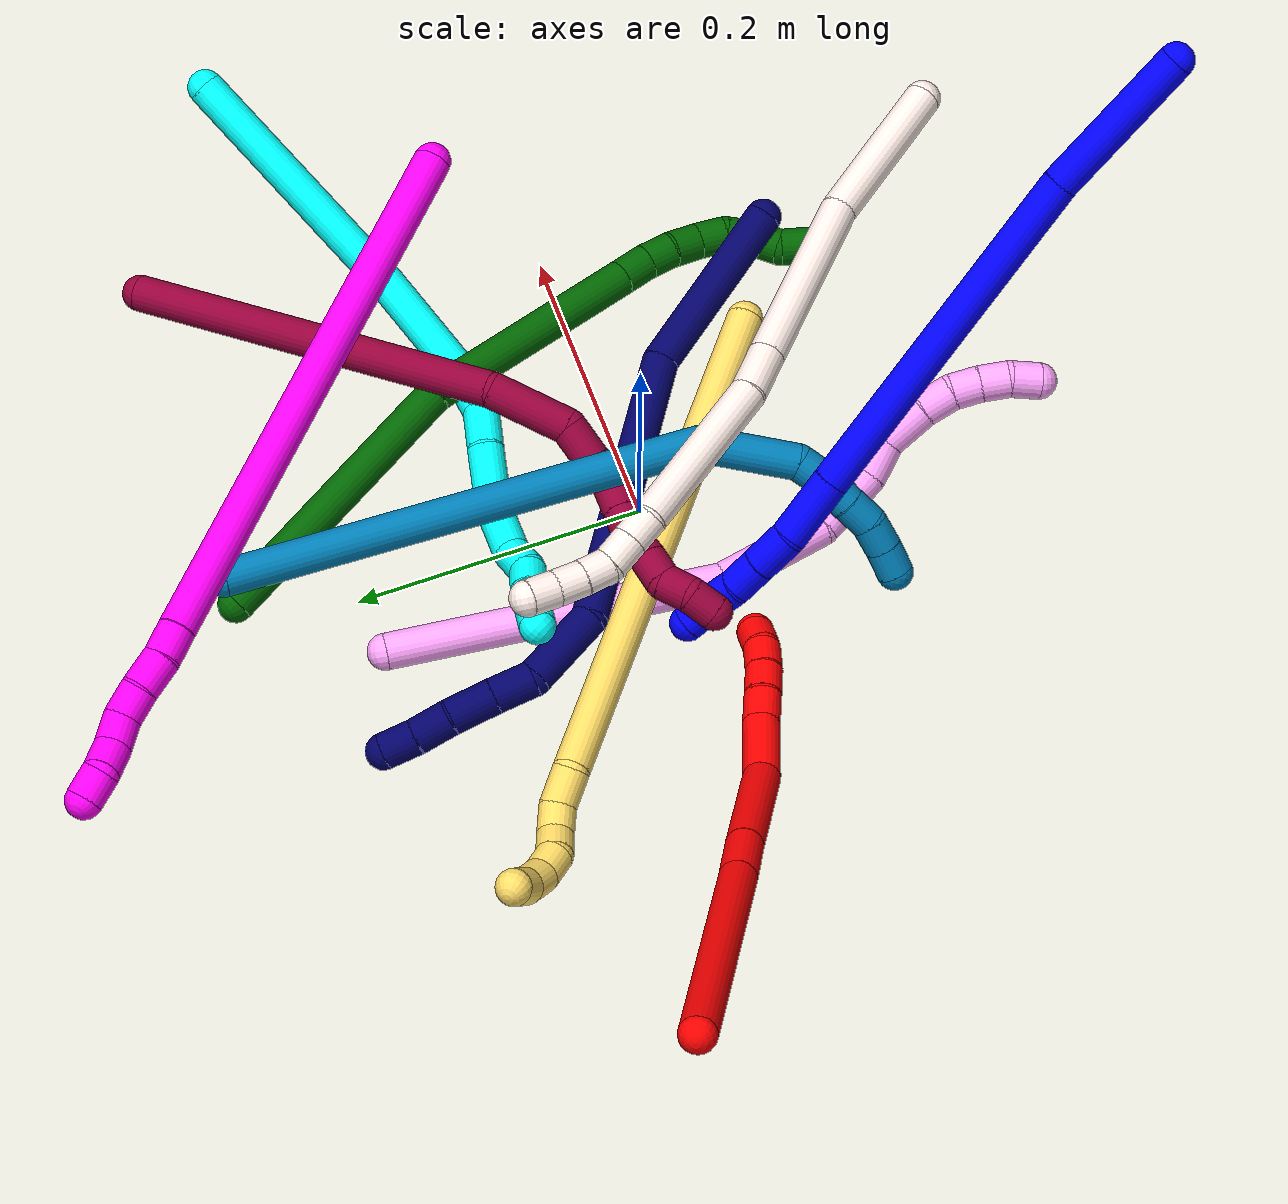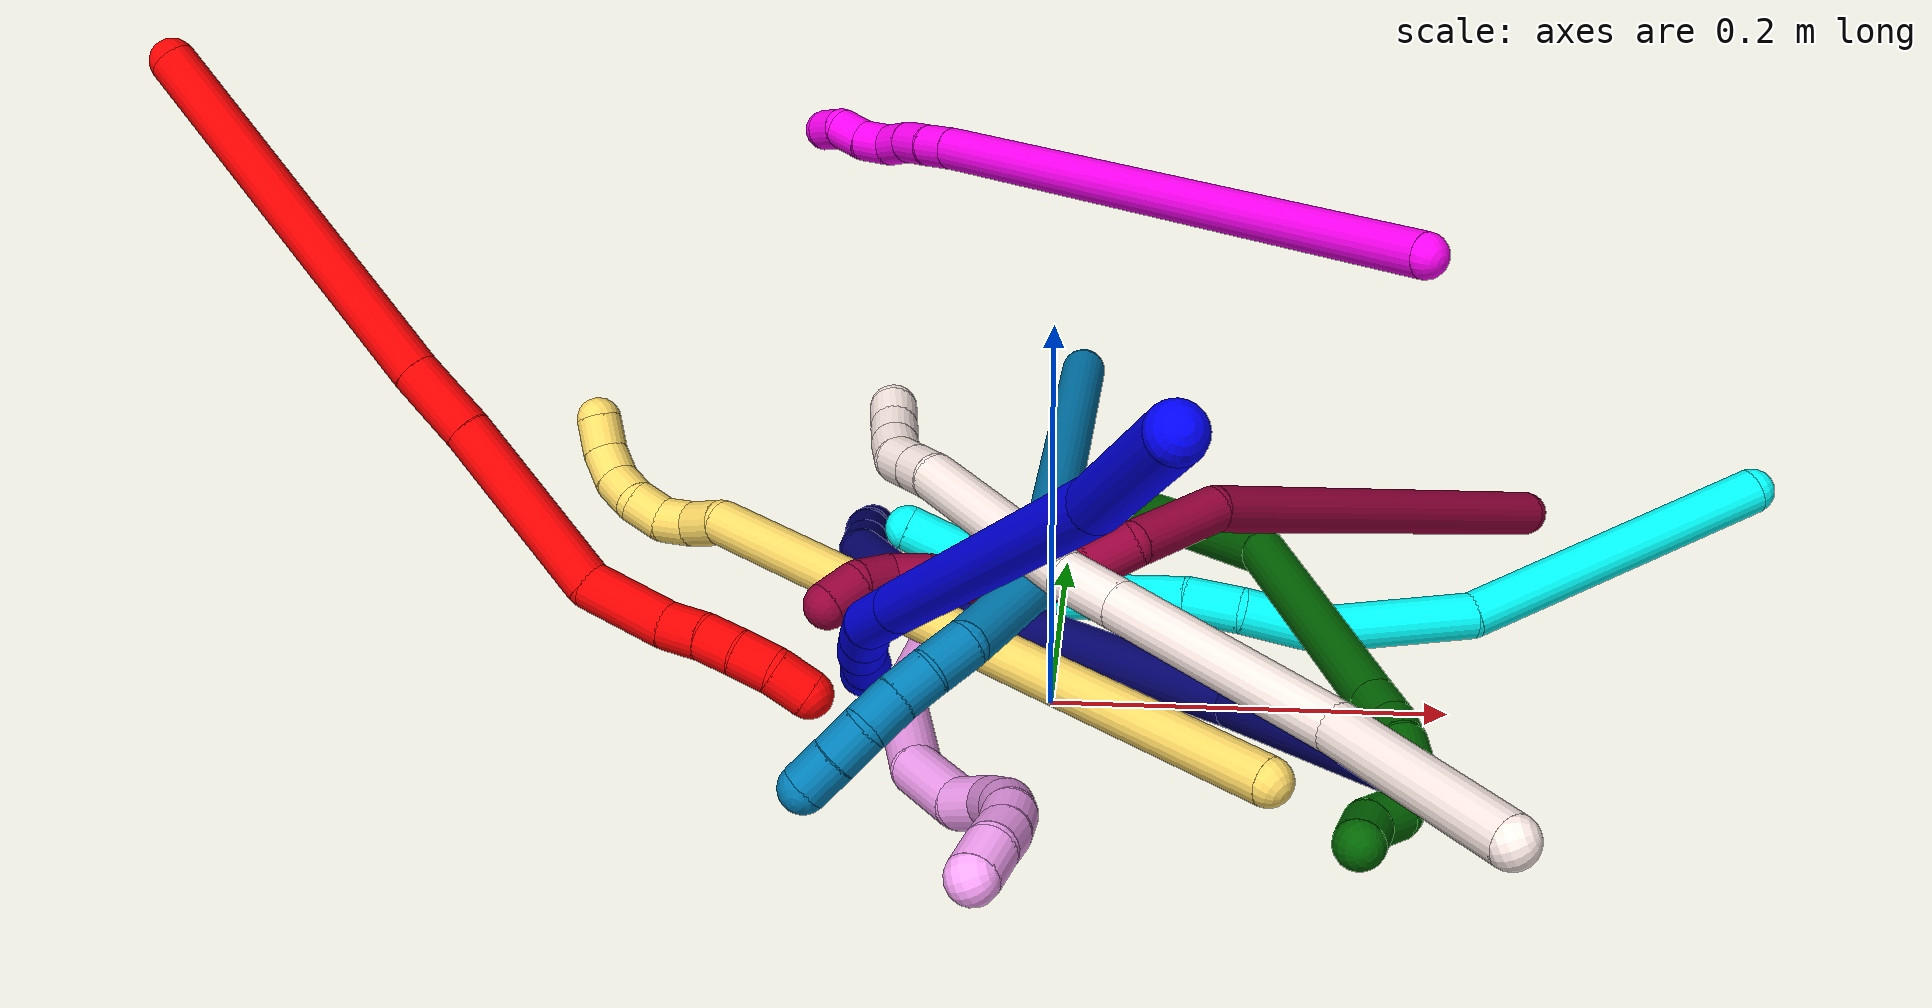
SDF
<sdf version="1.7">
 <world name="default">
  <plugin name="TubeGeneratorPlugin" filename="libtube_generator_plugin.so"/>
  <model name="photoneo_s_sensor">
   <static>1</static>
   <pose>0 0 2 1.57079 1.57079 3.14159</pose>
   <link name="link">
    <inertial><mass>0.1</mass></inertial>
    <sensor name="sensor" type="depth">
     <update_rate>30</update_rate>
     <camera>
      <horizontal_fov>1.22</horizontal_fov>
      <image><width>1920</width><height>1200</height><format>B8G8R8</format></image>
      <clip><near>0.1</near><far>4</far></clip>
      <depth_camera><output>points</output></depth_camera>
     </camera>
     <plugin name="camera_plugin" filename="libgazebo_ros_depth_camera.so">
      <baseline>0.2</baseline>
      <alwaysOn>1</alwaysOn>
      <updateRate>0.0</updateRate>
      <cameraName>camera_ir</cameraName>
      <imageTopicName>/camera/color/image_raw</imageTopicName>
      <cameraInfoTopicName>/camera/color/camera_info</cameraInfoTopicName>
      <depthImageTopicName>/camera/depth/image_raw</depthImageTopicName>
      <depthImageCameraInfoTopicName>/camera/depth/camera_info</depthImageCameraInfoTopicName>
      <pointCloudTopicName>/camera/depth/points</pointCloudTopicName>
      <frameName>fr_optical</frameName>
      <pointCloudCutoff>0.1</pointCloudCutoff>
      <pointCloudCutoffMax>2.0</pointCloudCutoffMax>
      <distortionK1>0</distortionK1>
      <distortionK2>0</distortionK2>
      <distortionK3>0</distortionK3>
      <distortionT1>0</distortionT1>
      <distortionT2>0</distortionT2>
      <CxPrime>0</CxPrime>
      <Cx>0</Cx>
      <Cy>0</Cy>
      <focalLength>0</focalLength>
      <hackBaseline>0</hackBaseline>
     </plugin>
    </sensor>
   </link>
  </model>
  <gravity>0 0 -9.8</gravity>
  <magnetic_field>6e-06 2.3e-05 -4.2e-05</magnetic_field>
  <atmosphere type="adiabatic"/>
  <physics name="default_physics" default="0" type="ode">
   <max_step_size>0.003</max_step_size>
   <real_time_factor>1</real_time_factor>
   <real_time_update_rate>1000</real_time_update_rate>
   <max_contacts>10000</max_contacts>
   <ode>
    <solver>
     <type>quick</type>
     <iters>100</iters>
     <sor>1.3</sor>
     <use_dynamic_moi_rescaling>0</use_dynamic_moi_rescaling>
    </solver>
    <constraints>
     <contact_max_correcting_vel>0</contact_max_correcting_vel>
     <contact_surface_layer>0.001</contact_surface_layer>
     <cfm>0</cfm>
     <erp>0.2</erp>
    </constraints>
   </ode>
  </physics>
  <scene><ambient>0.4 0.4 0.4 1</ambient><background>0.7 0.7 0.7 1</background><shadows>0</shadows></scene>
  <audio><device>default</device></audio>
  <spherical_coordinates>
   <surface_model>EARTH_WGS84</surface_model>
   <latitude_deg>0</latitude_deg>
   <longitude_deg>0</longitude_deg>
   <elevation>0</elevation>
   <heading_deg>0</heading_deg>
  </spherical_coordinates>
  <model name="bin">
   <static>1</static>
   <link name="bottom">
    <collision name="collision-bottom">
     <pose>0 0 -0.01 0 -0 0</pose>
     <geometry><box><size>0.8 0.6 0.02</size></box></geometry>
     <surface>
      <friction><ode><mu>100</mu><mu2>100</mu2></ode></friction>
      <contact><collide_bitmask>65535</collide_bitmask></contact>
     </surface>
    </collision>
   </link>
   <link name="west_wall">
    <collision name="collision-west_wall">
     <pose>-0.41 0 0.1 0 -0 0</pose>
     <geometry><box><size>0.02 0.6 0.2</size></box></geometry>
     <surface>
      <friction><ode><mu>100</mu><mu2>100</mu2></ode></friction>
      <contact><collide_bitmask>65535</collide_bitmask></contact>
     </surface>
    </collision>
   </link>
   <link name="east_wall">
    <collision name="collision-east_wall">
     <pose>0.41 0 0.1 0 -0 0</pose>
     <geometry><box><size>0.02 0.6 0.2</size></box></geometry>
     <surface>
      <friction><ode><mu>100</mu><mu2>100</mu2></ode></friction>
      <contact><collide_bitmask>65535</collide_bitmask></contact>
     </surface>
    </collision>
   </link>
   <link name="south_wall">
    <collision name="collision-south_wall">
     <pose>0 -0.31 0.1 0 -0 0</pose>
     <geometry><box><size>0.8 0.02 0.2</size></box></geometry>
     <surface>
      <friction><ode><mu>100</mu><mu2>100</mu2></ode></friction>
      <contact><collide_bitmask>65535</collide_bitmask></contact>
     </surface>
    </collision>
   </link>
   <link name="north_wall">
    <collision name="collision-north_wall">
     <pose>0 0.31 0.1 0 -0 0</pose>
     <geometry><box><size>0.8 0.02 0.2</size></box></geometry>
     <surface>
      <friction><ode><mu>100</mu><mu2>100</mu2></ode></friction>
      <contact><collide_bitmask>65535</collide_bitmask></contact>
     </surface>
    </collision>
   </link>
  </model>
  <model name="1">
   <static>0</static>
   <link name="1">
    <collision name="collision-cylinder-e_1_1_4">
     <pose>0.000722 0.001649 -0.055338 -3.11181 0.013037 -0.825103</pose>
     <geometry><cylinder><radius>0.0125</radius><length>0.110734</length></cylinder></geometry>
     <surface>
      <friction><ode><mu>1.16</mu><mu2>1.16</mu2><slip1>0</slip1><slip2>0</slip2></ode></friction>
      <contact><ode><kp>1e+06</kp><kd>1</kd><max_vel>0</max_vel><min_depth>0.001</min_depth></ode></contact>
     </surface>
    </collision>
    <visual name="visual-cylinder-e_1_1_4">
     <pose>0.000722 0.001649 -0.055338 -3.11181 0.013037 -0.825103</pose>
     <geometry><cylinder><radius>0.0125</radius><length>0.110734</length></cylinder></geometry>
     <material><ambient>0 0 1 1</ambient></material>
    </visual>
    <collision name="collision-cylinder-e_2_4_5">
     <pose>0.017258 0.013883 -0.233135 -3.05537 0.127954 -1.95636</pose>
     <geometry><cylinder><radius>0.0125</radius><length>0.247859</length></cylinder></geometry>
     <surface>
      <friction><ode><mu>1.16</mu><mu2>1.16</mu2><slip1>0</slip1><slip2>0</slip2></ode></friction>
      <contact><ode><kp>1e+06</kp><kd>1</kd><max_vel>0</max_vel><min_depth>0.001</min_depth></ode></contact>
     </surface>
    </collision>
    <visual name="visual-cylinder-e_2_4_5">
     <pose>0.017258 0.013883 -0.233135 -3.05537 0.127954 -1.95636</pose>
     <geometry><cylinder><radius>0.0125</radius><length>0.247859</length></cylinder></geometry>
     <material><ambient>0 0 1 1</ambient></material>
    </visual>
    <collision name="collision-cylinder-e_3_5_6">
     <pose>0.035889 0.026637 -0.378508 -3.04721 0.121799 -1.82357</pose>
     <geometry><cylinder><radius>0.0125</radius><length>0.046376</length></cylinder></geometry>
     <surface>
      <friction><ode><mu>1.16</mu><mu2>1.16</mu2><slip1>0</slip1><slip2>0</slip2></ode></friction>
      <contact><ode><kp>1e+06</kp><kd>1</kd><max_vel>0</max_vel><min_depth>0.001</min_depth></ode></contact>
     </surface>
    </collision>
    <visual name="visual-cylinder-e_3_5_6">
     <pose>0.035889 0.026637 -0.378508 -3.04721 0.121799 -1.82357</pose>
     <geometry><cylinder><radius>0.0125</radius><length>0.046376</length></cylinder></geometry>
     <material><ambient>0 0 1 1</ambient></material>
    </visual>
    <collision name="collision-cylinder-e_4_6_7">
     <pose>0.03717 0.029239 -0.415486 -3.11078 -0.108775 2.59007</pose>
     <geometry><cylinder><radius>0.0125</radius><length>0.028309</length></cylinder></geometry>
     <surface>
      <friction><ode><mu>1.16</mu><mu2>1.16</mu2><slip1>0</slip1><slip2>0</slip2></ode></friction>
      <contact><ode><kp>1e+06</kp><kd>1</kd><max_vel>0</max_vel><min_depth>0.001</min_depth></ode></contact>
     </surface>
    </collision>
    <visual name="visual-cylinder-e_4_6_7">
     <pose>0.03717 0.029239 -0.415486 -3.11078 -0.108775 2.59007</pose>
     <geometry><cylinder><radius>0.0125</radius><length>0.028309</length></cylinder></geometry>
     <material><ambient>0 0 1 1</ambient></material>
    </visual>
    <collision name="collision-cylinder-e_5_7_8">
     <pose>0.033938 0.030242 -0.44099 -3.09191 -0.146893 2.49027</pose>
     <geometry><cylinder><radius>0.0125</radius><length>0.023157</length></cylinder></geometry>
     <surface>
      <friction><ode><mu>1.16</mu><mu2>1.16</mu2><slip1>0</slip1><slip2>0</slip2></ode></friction>
      <contact><ode><kp>1e+06</kp><kd>1</kd><max_vel>0</max_vel><min_depth>0.001</min_depth></ode></contact>
     </surface>
    </collision>
    <visual name="visual-cylinder-e_5_7_8">
     <pose>0.033938 0.030242 -0.44099 -3.09191 -0.146893 2.49027</pose>
     <geometry><cylinder><radius>0.0125</radius><length>0.023157</length></cylinder></geometry>
     <material><ambient>0 0 1 1</ambient></material>
    </visual>
    <collision name="collision-cylinder-e_6_8_9">
     <pose>0.028719 0.030875 -0.462682 -3.13533 -0.331197 3.1041</pose>
     <geometry><cylinder><radius>0.0125</radius><length>0.021682</length></cylinder></geometry>
     <surface>
      <friction><ode><mu>1.16</mu><mu2>1.16</mu2><slip1>0</slip1><slip2>0</slip2></ode></friction>
      <contact><ode><kp>1e+06</kp><kd>1</kd><max_vel>0</max_vel><min_depth>0.001</min_depth></ode></contact>
     </surface>
    </collision>
    <visual name="visual-cylinder-e_6_8_9">
     <pose>0.028719 0.030875 -0.462682 -3.13533 -0.331197 3.1041</pose>
     <geometry><cylinder><radius>0.0125</radius><length>0.021682</length></cylinder></geometry>
     <material><ambient>0 0 1 1</ambient></material>
    </visual>
    <collision name="collision-cylinder-e_7_9_2">
     <pose>0.024468 0.030278 -0.483831 3.08104 -0.066335 -1.66189</pose>
     <geometry><cylinder><radius>0.0125</radius><length>0.021883</length></cylinder></geometry>
     <surface>
      <friction><ode><mu>1.16</mu><mu2>1.16</mu2><slip1>0</slip1><slip2>0</slip2></ode></friction>
      <contact><ode><kp>1e+06</kp><kd>1</kd><max_vel>0</max_vel><min_depth>0.001</min_depth></ode></contact>
     </surface>
    </collision>
    <visual name="visual-cylinder-e_7_9_2">
     <pose>0.024468 0.030278 -0.483831 3.08104 -0.066335 -1.66189</pose>
     <geometry><cylinder><radius>0.0125</radius><length>0.021883</length></cylinder></geometry>
     <material><ambient>0 0 1 1</ambient></material>
    </visual>
    <collision name="collision-sphere-2">
     <pose>0.023743 0.029617 -0.494728 0 -0 0</pose>
     <geometry><sphere><radius>0.0125</radius></sphere></geometry>
     <surface>
      <friction><ode><mu>1.16</mu><mu2>1.16</mu2><slip1>0</slip1><slip2>0</slip2></ode></friction>
      <contact><ode><kp>1e+06</kp><kd>1</kd><max_vel>0</max_vel><min_depth>0.001</min_depth></ode></contact>
     </surface>
    </collision>
    <visual name="visual-sphere-2">
     <pose>0.023743 0.029617 -0.494728 0 -0 0</pose>
     <geometry><sphere><radius>0.0125</radius></sphere></geometry>
     <material><ambient>0 0 1 1</ambient></material>
    </visual>
    <collision name="collision-sphere-9">
     <pose>0.025193 0.030939 -0.472933 0 -0 0</pose>
     <geometry><sphere><radius>0.0125</radius></sphere></geometry>
     <surface>
      <friction><ode><mu>1.16</mu><mu2>1.16</mu2><slip1>0</slip1><slip2>0</slip2></ode></friction>
      <contact><ode><kp>1e+06</kp><kd>1</kd><max_vel>0</max_vel><min_depth>0.001</min_depth></ode></contact>
     </surface>
    </collision>
    <visual name="visual-sphere-9">
     <pose>0.025193 0.030939 -0.472933 0 -0 0</pose>
     <geometry><sphere><radius>0.0125</radius></sphere></geometry>
     <material><ambient>0 0 1 1</ambient></material>
    </visual>
    <collision name="collision-sphere-4">
     <pose>0.001444 0.003298 -0.110675 0 -0 0</pose>
     <geometry><sphere><radius>0.0125</radius></sphere></geometry>
     <surface>
      <friction><ode><mu>1.16</mu><mu2>1.16</mu2><slip1>0</slip1><slip2>0</slip2></ode></friction>
      <contact><ode><kp>1e+06</kp><kd>1</kd><max_vel>0</max_vel><min_depth>0.001</min_depth></ode></contact>
     </surface>
    </collision>
    <visual name="visual-sphere-4">
     <pose>0.001444 0.003298 -0.110675 0 -0 0</pose>
     <geometry><sphere><radius>0.0125</radius></sphere></geometry>
     <material><ambient>0 0 1 1</ambient></material>
    </visual>
    <collision name="collision-sphere-1">
     <geometry><sphere><radius>0.0125</radius></sphere></geometry>
     <surface>
      <friction><ode><mu>1.16</mu><mu2>1.16</mu2><slip1>0</slip1><slip2>0</slip2></ode></friction>
      <contact><ode><kp>1e+06</kp><kd>1</kd><max_vel>0</max_vel><min_depth>0.001</min_depth></ode></contact>
     </surface>
    </collision>
    <visual name="visual-sphere-1">
     <geometry><sphere><radius>0.0125</radius></sphere></geometry>
     <material><ambient>0 0 1 1</ambient></material>
    </visual>
    <collision name="collision-sphere-8">
     <pose>0.032244 0.03081 -0.45243 0 -0 0</pose>
     <geometry><sphere><radius>0.0125</radius></sphere></geometry>
     <surface>
      <friction><ode><mu>1.16</mu><mu2>1.16</mu2><slip1>0</slip1><slip2>0</slip2></ode></friction>
      <contact><ode><kp>1e+06</kp><kd>1</kd><max_vel>0</max_vel><min_depth>0.001</min_depth></ode></contact>
     </surface>
    </collision>
    <visual name="visual-sphere-8">
     <pose>0.032244 0.03081 -0.45243 0 -0 0</pose>
     <geometry><sphere><radius>0.0125</radius></sphere></geometry>
     <material><ambient>0 0 1 1</ambient></material>
    </visual>
    <collision name="collision-sphere-5">
     <pose>0.033072 0.024468 -0.355595 0 -0 0</pose>
     <geometry><sphere><radius>0.0125</radius></sphere></geometry>
     <surface>
      <friction><ode><mu>1.16</mu><mu2>1.16</mu2><slip1>0</slip1><slip2>0</slip2></ode></friction>
      <contact><ode><kp>1e+06</kp><kd>1</kd><max_vel>0</max_vel><min_depth>0.001</min_depth></ode></contact>
     </surface>
    </collision>
    <visual name="visual-sphere-5">
     <pose>0.033072 0.024468 -0.355595 0 -0 0</pose>
     <geometry><sphere><radius>0.0125</radius></sphere></geometry>
     <material><ambient>0 0 1 1</ambient></material>
    </visual>
    <collision name="collision-sphere-6">
     <pose>0.038706 0.028806 -0.401422 0 -0 0</pose>
     <geometry><sphere><radius>0.0125</radius></sphere></geometry>
     <surface>
      <friction><ode><mu>1.16</mu><mu2>1.16</mu2><slip1>0</slip1><slip2>0</slip2></ode></friction>
      <contact><ode><kp>1e+06</kp><kd>1</kd><max_vel>0</max_vel><min_depth>0.001</min_depth></ode></contact>
     </surface>
    </collision>
    <visual name="visual-sphere-6">
     <pose>0.038706 0.028806 -0.401422 0 -0 0</pose>
     <geometry><sphere><radius>0.0125</radius></sphere></geometry>
     <material><ambient>0 0 1 1</ambient></material>
    </visual>
    <collision name="collision-sphere-7">
     <pose>0.035633 0.029673 -0.429551 0 -0 0</pose>
     <geometry><sphere><radius>0.0125</radius></sphere></geometry>
     <surface>
      <friction><ode><mu>1.16</mu><mu2>1.16</mu2><slip1>0</slip1><slip2>0</slip2></ode></friction>
      <contact><ode><kp>1e+06</kp><kd>1</kd><max_vel>0</max_vel><min_depth>0.001</min_depth></ode></contact>
     </surface>
    </collision>
    <visual name="visual-sphere-7">
     <pose>0.035633 0.029673 -0.429551 0 -0 0</pose>
     <geometry><sphere><radius>0.0125</radius></sphere></geometry>
     <material><ambient>0 0 1 1</ambient></material>
    </visual>
    <inertial>
     <pose>0.018036 0.015438 -0.248119 0 -0 0</pose>
     <mass>0.5</mass>
     <inertia>
      <ixx>-0.001674</ixx>
      <ixy>0</ixy>
      <ixz>0</ixz>
      <iyy>-0.000847</iyy>
      <iyz>0</iyz>
      <izz>-0.000317</izz>
     </inertia>
    </inertial>
   </link>
   <pose>0.060626 -0.391976 0.274381 -0.891632 -0.606408 2.9998</pose>
  </model>
  <model name="2">
   <static>0</static>
   <link name="2">
    <collision name="collision-cylinder-e_1_1_4">
     <pose>0.000165 -3.2e-05 -0.110597 3.1413 0.00149 2.75802</pose>
     <geometry><cylinder><radius>0.0125</radius><length>0.221195</length></cylinder></geometry>
     <surface>
      <friction><ode><mu>1.16</mu><mu2>1.16</mu2><slip1>0</slip1><slip2>0</slip2></ode></friction>
      <contact><ode><kp>1e+06</kp><kd>1</kd><max_vel>0</max_vel><min_depth>0.001</min_depth></ode></contact>
     </surface>
    </collision>
    <visual name="visual-cylinder-e_1_1_4">
     <pose>0.000165 -3.2e-05 -0.110597 3.1413 0.00149 2.75802</pose>
     <geometry><cylinder><radius>0.0125</radius><length>0.221195</length></cylinder></geometry>
     <material><ambient>1 0 0 1</ambient></material>
    </visual>
    <collision name="collision-cylinder-e_2_4_5">
     <pose>0.001289 -0.001147 -0.242549 3.09092 0.044843 1.44883</pose>
     <geometry><cylinder><radius>0.0125</radius><length>0.042808</length></cylinder></geometry>
     <surface>
      <friction><ode><mu>1.16</mu><mu2>1.16</mu2><slip1>0</slip1><slip2>0</slip2></ode></friction>
      <contact><ode><kp>1e+06</kp><kd>1</kd><max_vel>0</max_vel><min_depth>0.001</min_depth></ode></contact>
     </surface>
    </collision>
    <visual name="visual-cylinder-e_2_4_5">
     <pose>0.001289 -0.001147 -0.242549 3.09092 0.044843 1.44883</pose>
     <geometry><cylinder><radius>0.0125</radius><length>0.042808</length></cylinder></geometry>
     <material><ambient>1 0 0 1</ambient></material>
    </visual>
    <collision name="collision-cylinder-e_3_5_6">
     <pose>0.002516 -0.002469 -0.316014 3.13701 0.005136 1.68363</pose>
     <geometry><cylinder><radius>0.0125</radius><length>0.104222</length></cylinder></geometry>
     <surface>
      <friction><ode><mu>1.16</mu><mu2>1.16</mu2><slip1>0</slip1><slip2>0</slip2></ode></friction>
      <contact><ode><kp>1e+06</kp><kd>1</kd><max_vel>0</max_vel><min_depth>0.001</min_depth></ode></contact>
     </surface>
    </collision>
    <visual name="visual-cylinder-e_3_5_6">
     <pose>0.002516 -0.002469 -0.316014 3.13701 0.005136 1.68363</pose>
     <geometry><cylinder><radius>0.0125</radius><length>0.104222</length></cylinder></geometry>
     <material><ambient>1 0 0 1</ambient></material>
    </visual>
    <collision name="collision-cylinder-e_4_6_7">
     <pose>0.009808 -0.009722 -0.389852 2.82933 0.298461 1.5249</pose>
     <geometry><cylinder><radius>0.0125</radius><length>0.047777</length></cylinder></geometry>
     <surface>
      <friction><ode><mu>1.16</mu><mu2>1.16</mu2><slip1>0</slip1><slip2>0</slip2></ode></friction>
      <contact><ode><kp>1e+06</kp><kd>1</kd><max_vel>0</max_vel><min_depth>0.001</min_depth></ode></contact>
     </surface>
    </collision>
    <visual name="visual-cylinder-e_4_6_7">
     <pose>0.009808 -0.009722 -0.389852 2.82933 0.298461 1.5249</pose>
     <geometry><cylinder><radius>0.0125</radius><length>0.047777</length></cylinder></geometry>
     <material><ambient>1 0 0 1</ambient></material>
    </visual>
    <collision name="collision-cylinder-e_5_7_8">
     <pose>0.02054 -0.022114 -0.420393 2.59374 0.344787 1.10952</pose>
     <geometry><cylinder><radius>0.0125</radius><length>0.021938</length></cylinder></geometry>
     <surface>
      <friction><ode><mu>1.16</mu><mu2>1.16</mu2><slip1>0</slip1><slip2>0</slip2></ode></friction>
      <contact><ode><kp>1e+06</kp><kd>1</kd><max_vel>0</max_vel><min_depth>0.001</min_depth></ode></contact>
     </surface>
    </collision>
    <visual name="visual-cylinder-e_5_7_8">
     <pose>0.02054 -0.022114 -0.420393 2.59374 0.344787 1.10952</pose>
     <geometry><cylinder><radius>0.0125</radius><length>0.021938</length></cylinder></geometry>
     <material><ambient>1 0 0 1</ambient></material>
    </visual>
    <collision name="collision-cylinder-e_6_8_9">
     <pose>0.027175 -0.031236 -0.438207 2.74734 0.291647 1.26812</pose>
     <geometry><cylinder><radius>0.0125</radius><length>0.020358</length></cylinder></geometry>
     <surface>
      <friction><ode><mu>1.16</mu><mu2>1.16</mu2><slip1>0</slip1><slip2>0</slip2></ode></friction>
      <contact><ode><kp>1e+06</kp><kd>1</kd><max_vel>0</max_vel><min_depth>0.001</min_depth></ode></contact>
     </surface>
    </collision>
    <visual name="visual-cylinder-e_6_8_9">
     <pose>0.027175 -0.031236 -0.438207 2.74734 0.291647 1.26812</pose>
     <geometry><cylinder><radius>0.0125</radius><length>0.020358</length></cylinder></geometry>
     <material><ambient>1 0 0 1</ambient></material>
    </visual>
    <collision name="collision-cylinder-e_7_9_10">
     <pose>0.033616 -0.037515 -0.456555 2.87683 0.348121 1.8453</pose>
     <geometry><cylinder><radius>0.0125</radius><length>0.020605</length></cylinder></geometry>
     <surface>
      <friction><ode><mu>1.16</mu><mu2>1.16</mu2><slip1>0</slip1><slip2>0</slip2></ode></friction>
      <contact><ode><kp>1e+06</kp><kd>1</kd><max_vel>0</max_vel><min_depth>0.001</min_depth></ode></contact>
     </surface>
    </collision>
    <visual name="visual-cylinder-e_7_9_10">
     <pose>0.033616 -0.037515 -0.456555 2.87683 0.348121 1.8453</pose>
     <geometry><cylinder><radius>0.0125</radius><length>0.020605</length></cylinder></geometry>
     <material><ambient>1 0 0 1</ambient></material>
    </visual>
    <collision name="collision-cylinder-e_8_10_2">
     <pose>0.040758 -0.039735 -0.475802 -3.1099 0.351065 -2.96334</pose>
     <geometry><cylinder><radius>0.0125</radius><length>0.021098</length></cylinder></geometry>
     <surface>
      <friction><ode><mu>1.16</mu><mu2>1.16</mu2><slip1>0</slip1><slip2>0</slip2></ode></friction>
      <contact><ode><kp>1e+06</kp><kd>1</kd><max_vel>0</max_vel><min_depth>0.001</min_depth></ode></contact>
     </surface>
    </collision>
    <visual name="visual-cylinder-e_8_10_2">
     <pose>0.040758 -0.039735 -0.475802 -3.1099 0.351065 -2.96334</pose>
     <geometry><cylinder><radius>0.0125</radius><length>0.021098</length></cylinder></geometry>
     <material><ambient>1 0 0 1</ambient></material>
    </visual>
    <collision name="collision-sphere-2">
     <pose>0.044386 -0.039422 -0.485703 0 -0 0</pose>
     <geometry><sphere><radius>0.0125</radius></sphere></geometry>
     <surface>
      <friction><ode><mu>1.16</mu><mu2>1.16</mu2><slip1>0</slip1><slip2>0</slip2></ode></friction>
      <contact><ode><kp>1e+06</kp><kd>1</kd><max_vel>0</max_vel><min_depth>0.001</min_depth></ode></contact>
     </surface>
    </collision>
    <visual name="visual-sphere-2">
     <pose>0.044386 -0.039422 -0.485703 0 -0 0</pose>
     <geometry><sphere><radius>0.0125</radius></sphere></geometry>
     <material><ambient>1 0 0 1</ambient></material>
    </visual>
    <collision name="collision-sphere-10">
     <pose>0.03713 -0.040049 -0.465902 0 -0 0</pose>
     <geometry><sphere><radius>0.0125</radius></sphere></geometry>
     <surface>
      <friction><ode><mu>1.16</mu><mu2>1.16</mu2><slip1>0</slip1><slip2>0</slip2></ode></friction>
      <contact><ode><kp>1e+06</kp><kd>1</kd><max_vel>0</max_vel><min_depth>0.001</min_depth></ode></contact>
     </surface>
    </collision>
    <visual name="visual-sphere-10">
     <pose>0.03713 -0.040049 -0.465902 0 -0 0</pose>
     <geometry><sphere><radius>0.0125</radius></sphere></geometry>
     <material><ambient>1 0 0 1</ambient></material>
    </visual>
    <collision name="collision-sphere-9">
     <pose>0.030101 -0.034981 -0.447208 0 -0 0</pose>
     <geometry><sphere><radius>0.0125</radius></sphere></geometry>
     <surface>
      <friction><ode><mu>1.16</mu><mu2>1.16</mu2><slip1>0</slip1><slip2>0</slip2></ode></friction>
      <contact><ode><kp>1e+06</kp><kd>1</kd><max_vel>0</max_vel><min_depth>0.001</min_depth></ode></contact>
     </surface>
    </collision>
    <visual name="visual-sphere-9">
     <pose>0.030101 -0.034981 -0.447208 0 -0 0</pose>
     <geometry><sphere><radius>0.0125</radius></sphere></geometry>
     <material><ambient>1 0 0 1</ambient></material>
    </visual>
    <collision name="collision-sphere-4">
     <pose>0.00033 -6.4e-05 -0.221194 0 -0 0</pose>
     <geometry><sphere><radius>0.0125</radius></sphere></geometry>
     <surface>
      <friction><ode><mu>1.16</mu><mu2>1.16</mu2><slip1>0</slip1><slip2>0</slip2></ode></friction>
      <contact><ode><kp>1e+06</kp><kd>1</kd><max_vel>0</max_vel><min_depth>0.001</min_depth></ode></contact>
     </surface>
    </collision>
    <visual name="visual-sphere-4">
     <pose>0.00033 -6.4e-05 -0.221194 0 -0 0</pose>
     <geometry><sphere><radius>0.0125</radius></sphere></geometry>
     <material><ambient>1 0 0 1</ambient></material>
    </visual>
    <collision name="collision-sphere-1">
     <geometry><sphere><radius>0.0125</radius></sphere></geometry>
     <surface>
      <friction><ode><mu>1.16</mu><mu2>1.16</mu2><slip1>0</slip1><slip2>0</slip2></ode></friction>
      <contact><ode><kp>1e+06</kp><kd>1</kd><max_vel>0</max_vel><min_depth>0.001</min_depth></ode></contact>
     </surface>
    </collision>
    <visual name="visual-sphere-1">
     <geometry><sphere><radius>0.0125</radius></sphere></geometry>
     <material><ambient>1 0 0 1</ambient></material>
    </visual>
    <collision name="collision-sphere-8">
     <pose>0.024248 -0.027491 -0.429205 0 -0 0</pose>
     <geometry><sphere><radius>0.0125</radius></sphere></geometry>
     <surface>
      <friction><ode><mu>1.16</mu><mu2>1.16</mu2><slip1>0</slip1><slip2>0</slip2></ode></friction>
      <contact><ode><kp>1e+06</kp><kd>1</kd><max_vel>0</max_vel><min_depth>0.001</min_depth></ode></contact>
     </surface>
    </collision>
    <visual name="visual-sphere-8">
     <pose>0.024248 -0.027491 -0.429205 0 -0 0</pose>
     <geometry><sphere><radius>0.0125</radius></sphere></geometry>
     <material><ambient>1 0 0 1</ambient></material>
    </visual>
    <collision name="collision-sphere-5">
     <pose>0.002249 -0.00223 -0.263905 0 -0 0</pose>
     <geometry><sphere><radius>0.0125</radius></sphere></geometry>
     <surface>
      <friction><ode><mu>1.16</mu><mu2>1.16</mu2><slip1>0</slip1><slip2>0</slip2></ode></friction>
      <contact><ode><kp>1e+06</kp><kd>1</kd><max_vel>0</max_vel><min_depth>0.001</min_depth></ode></contact>
     </surface>
    </collision>
    <visual name="visual-sphere-5">
     <pose>0.002249 -0.00223 -0.263905 0 -0 0</pose>
     <geometry><sphere><radius>0.0125</radius></sphere></geometry>
     <material><ambient>1 0 0 1</ambient></material>
    </visual>
    <collision name="collision-sphere-6">
     <pose>0.002784 -0.002708 -0.368124 0 -0 0</pose>
     <geometry><sphere><radius>0.0125</radius></sphere></geometry>
     <surface>
      <friction><ode><mu>1.16</mu><mu2>1.16</mu2><slip1>0</slip1><slip2>0</slip2></ode></friction>
      <contact><ode><kp>1e+06</kp><kd>1</kd><max_vel>0</max_vel><min_depth>0.001</min_depth></ode></contact>
     </surface>
    </collision>
    <visual name="visual-sphere-6">
     <pose>0.002784 -0.002708 -0.368124 0 -0 0</pose>
     <geometry><sphere><radius>0.0125</radius></sphere></geometry>
     <material><ambient>1 0 0 1</ambient></material>
    </visual>
    <collision name="collision-sphere-7">
     <pose>0.016833 -0.016737 -0.41158 0 -0 0</pose>
     <geometry><sphere><radius>0.0125</radius></sphere></geometry>
     <surface>
      <friction><ode><mu>1.16</mu><mu2>1.16</mu2><slip1>0</slip1><slip2>0</slip2></ode></friction>
      <contact><ode><kp>1e+06</kp><kd>1</kd><max_vel>0</max_vel><min_depth>0.001</min_depth></ode></contact>
     </surface>
    </collision>
    <visual name="visual-sphere-7">
     <pose>0.016833 -0.016737 -0.41158 0 -0 0</pose>
     <geometry><sphere><radius>0.0125</radius></sphere></geometry>
     <material><ambient>1 0 0 1</ambient></material>
    </visual>
    <inertial>
     <pose>0.006758 -0.007021 -0.247994 0 -0 0</pose>
     <mass>0.5</mass>
     <inertia>
      <ixx>-0.00039</ixx>
      <ixy>0</ixy>
      <ixz>0</ixz>
      <iyy>0.001314</iyy>
      <iyz>0</iyz>
      <izz>-3.9e-05</izz>
     </inertia>
    </inertial>
   </link>
   <pose>-0.479327 0.137658 0.297144 -0.805916 -0.311049 0.769301</pose>
  </model>
  <model name="3">
   <static>0</static>
   <link name="3">
    <collision name="collision-cylinder-e_1_1_4">
     <pose>-0.007227 0.005141 -0.089758 -3.08438 -0.080208 1.9027</pose>
     <geometry><cylinder><radius>0.0125</radius><length>0.18039</length></cylinder></geometry>
     <surface>
      <friction><ode><mu>1.16</mu><mu2>1.16</mu2><slip1>0</slip1><slip2>0</slip2></ode></friction>
      <contact><ode><kp>1e+06</kp><kd>1</kd><max_vel>0</max_vel><min_depth>0.001</min_depth></ode></contact>
     </surface>
    </collision>
    <visual name="visual-cylinder-e_1_1_4">
     <pose>-0.007227 0.005141 -0.089758 -3.08438 -0.080208 1.9027</pose>
     <geometry><cylinder><radius>0.0125</radius><length>0.18039</length></cylinder></geometry>
     <material><ambient>0.003922 1 0.996078 1</ambient></material>
    </visual>
    <collision name="collision-cylinder-e_2_4_5">
     <pose>-0.030739 0.012932 -0.219505 -3.07539 -0.385987 2.80589</pose>
     <geometry><cylinder><radius>0.0125</radius><length>0.08652</length></cylinder></geometry>
     <surface>
      <friction><ode><mu>1.16</mu><mu2>1.16</mu2><slip1>0</slip1><slip2>0</slip2></ode></friction>
      <contact><ode><kp>1e+06</kp><kd>1</kd><max_vel>0</max_vel><min_depth>0.001</min_depth></ode></contact>
     </surface>
    </collision>
    <visual name="visual-cylinder-e_2_4_5">
     <pose>-0.030739 0.012932 -0.219505 -3.07539 -0.385987 2.80589</pose>
     <geometry><cylinder><radius>0.0125</radius><length>0.08652</length></cylinder></geometry>
     <material><ambient>0.003922 1 0.996078 1</ambient></material>
    </visual>
    <collision name="collision-cylinder-e_3_5_6">
     <pose>-0.060938 0.018299 -0.275225 -2.97066 -0.716851 2.69192</pose>
     <geometry><cylinder><radius>0.0125</radius><length>0.042349</length></cylinder></geometry>
     <surface>
      <friction><ode><mu>1.16</mu><mu2>1.16</mu2><slip1>0</slip1><slip2>0</slip2></ode></friction>
      <contact><ode><kp>1e+06</kp><kd>1</kd><max_vel>0</max_vel><min_depth>0.001</min_depth></ode></contact>
     </surface>
    </collision>
    <visual name="visual-cylinder-e_3_5_6">
     <pose>-0.060938 0.018299 -0.275225 -2.97066 -0.716851 2.69192</pose>
     <geometry><cylinder><radius>0.0125</radius><length>0.042349</length></cylinder></geometry>
     <material><ambient>0.003922 1 0.996078 1</ambient></material>
    </visual>
    <collision name="collision-cylinder-e_4_6_7">
     <pose>-0.084 0.027866 -0.300869 -2.53684 -0.649417 1.64688</pose>
     <geometry><cylinder><radius>0.0125</radius><length>0.030262</length></cylinder></geometry>
     <surface>
      <friction><ode><mu>1.16</mu><mu2>1.16</mu2><slip1>0</slip1><slip2>0</slip2></ode></friction>
      <contact><ode><kp>1e+06</kp><kd>1</kd><max_vel>0</max_vel><min_depth>0.001</min_depth></ode></contact>
     </surface>
    </collision>
    <visual name="visual-cylinder-e_4_6_7">
     <pose>-0.084 0.027866 -0.300869 -2.53684 -0.649417 1.64688</pose>
     <geometry><cylinder><radius>0.0125</radius><length>0.030262</length></cylinder></geometry>
     <material><ambient>0.003922 1 0.996078 1</ambient></material>
    </visual>
    <collision name="collision-cylinder-e_5_7_8">
     <pose>-0.103274 0.04606 -0.326653 -2.52106 -0.478754 1.30125</pose>
     <geometry><cylinder><radius>0.0125</radius><length>0.043957</length></cylinder></geometry>
     <surface>
      <friction><ode><mu>1.16</mu><mu2>1.16</mu2><slip1>0</slip1><slip2>0</slip2></ode></friction>
      <contact><ode><kp>1e+06</kp><kd>1</kd><max_vel>0</max_vel><min_depth>0.001</min_depth></ode></contact>
     </surface>
    </collision>
    <visual name="visual-cylinder-e_5_7_8">
     <pose>-0.103274 0.04606 -0.326653 -2.52106 -0.478754 1.30125</pose>
     <geometry><cylinder><radius>0.0125</radius><length>0.043957</length></cylinder></geometry>
     <material><ambient>0.003922 1 0.996078 1</ambient></material>
    </visual>
    <collision name="collision-cylinder-e_6_8_9">
     <pose>-0.12203 0.062608 -0.356837 -2.79285 -0.51559 1.96356</pose>
     <geometry><cylinder><radius>0.0125</radius><length>0.035011</length></cylinder></geometry>
     <surface>
      <friction><ode><mu>1.16</mu><mu2>1.16</mu2><slip1>0</slip1><slip2>0</slip2></ode></friction>
      <contact><ode><kp>1e+06</kp><kd>1</kd><max_vel>0</max_vel><min_depth>0.001</min_depth></ode></contact>
     </surface>
    </collision>
    <visual name="visual-cylinder-e_6_8_9">
     <pose>-0.12203 0.062608 -0.356837 -2.79285 -0.51559 1.96356</pose>
     <geometry><cylinder><radius>0.0125</radius><length>0.035011</length></cylinder></geometry>
     <material><ambient>0.003922 1 0.996078 1</ambient></material>
    </visual>
    <collision name="collision-cylinder-e_7_9_10">
     <pose>-0.139934 0.06681 -0.379211 3.01791 -0.851327 -2.87013</pose>
     <geometry><cylinder><radius>0.0125</radius><length>0.024655</length></cylinder></geometry>
     <surface>
      <friction><ode><mu>1.16</mu><mu2>1.16</mu2><slip1>0</slip1><slip2>0</slip2></ode></friction>
      <contact><ode><kp>1e+06</kp><kd>1</kd><max_vel>0</max_vel><min_depth>0.001</min_depth></ode></contact>
     </surface>
    </collision>
    <visual name="visual-cylinder-e_7_9_10">
     <pose>-0.139934 0.06681 -0.379211 3.01791 -0.851327 -2.87013</pose>
     <geometry><cylinder><radius>0.0125</radius><length>0.024655</length></cylinder></geometry>
     <material><ambient>0.003922 1 0.996078 1</ambient></material>
    </visual>
    <collision name="collision-cylinder-e_8_10_11">
     <pose>-0.158354 0.069106 -0.392086 -2.54075 -1.00299 2.11291</pose>
     <geometry><cylinder><radius>0.0125</radius><length>0.021701</length></cylinder></geometry>
     <surface>
      <friction><ode><mu>1.16</mu><mu2>1.16</mu2><slip1>0</slip1><slip2>0</slip2></ode></friction>
      <contact><ode><kp>1e+06</kp><kd>1</kd><max_vel>0</max_vel><min_depth>0.001</min_depth></ode></contact>
     </surface>
    </collision>
    <visual name="visual-cylinder-e_8_10_11">
     <pose>-0.158354 0.069106 -0.392086 -2.54075 -1.00299 2.11291</pose>
     <geometry><cylinder><radius>0.0125</radius><length>0.021701</length></cylinder></geometry>
     <material><ambient>0.003922 1 0.996078 1</ambient></material>
    </visual>
    <collision name="collision-cylinder-e_9_11_2">
     <pose>-0.181442 0.076539 -0.406777 -2.74525 -0.915804 2.36777</pose>
     <geometry><cylinder><radius>0.0125</radius><length>0.035155</length></cylinder></geometry>
     <surface>
      <friction><ode><mu>1.16</mu><mu2>1.16</mu2><slip1>0</slip1><slip2>0</slip2></ode></friction>
      <contact><ode><kp>1e+06</kp><kd>1</kd><max_vel>0</max_vel><min_depth>0.001</min_depth></ode></contact>
     </surface>
    </collision>
    <visual name="visual-cylinder-e_9_11_2">
     <pose>-0.181442 0.076539 -0.406777 -2.74525 -0.915804 2.36777</pose>
     <geometry><cylinder><radius>0.0125</radius><length>0.035155</length></cylinder></geometry>
     <material><ambient>0.003922 1 0.996078 1</ambient></material>
    </visual>
    <collision name="collision-sphere-2">
     <pose>-0.195382 0.080672 -0.416654 0 -0 0</pose>
     <geometry><sphere><radius>0.0125</radius></sphere></geometry>
     <surface>
      <friction><ode><mu>1.16</mu><mu2>1.16</mu2><slip1>0</slip1><slip2>0</slip2></ode></friction>
      <contact><ode><kp>1e+06</kp><kd>1</kd><max_vel>0</max_vel><min_depth>0.001</min_depth></ode></contact>
     </surface>
    </collision>
    <visual name="visual-sphere-2">
     <pose>-0.195382 0.080672 -0.416654 0 -0 0</pose>
     <geometry><sphere><radius>0.0125</radius></sphere></geometry>
     <material><ambient>0.003922 1 0.996078 1</ambient></material>
    </visual>
    <collision name="collision-sphere-11">
     <pose>-0.167502 0.072405 -0.3969 0 -0 0</pose>
     <geometry><sphere><radius>0.0125</radius></sphere></geometry>
     <surface>
      <friction><ode><mu>1.16</mu><mu2>1.16</mu2><slip1>0</slip1><slip2>0</slip2></ode></friction>
      <contact><ode><kp>1e+06</kp><kd>1</kd><max_vel>0</max_vel><min_depth>0.001</min_depth></ode></contact>
     </surface>
    </collision>
    <visual name="visual-sphere-11">
     <pose>-0.167502 0.072405 -0.3969 0 -0 0</pose>
     <geometry><sphere><radius>0.0125</radius></sphere></geometry>
     <material><ambient>0.003922 1 0.996078 1</ambient></material>
    </visual>
    <collision name="collision-sphere-10">
     <pose>-0.149206 0.065807 -0.387273 0 -0 0</pose>
     <geometry><sphere><radius>0.0125</radius></sphere></geometry>
     <surface>
      <friction><ode><mu>1.16</mu><mu2>1.16</mu2><slip1>0</slip1><slip2>0</slip2></ode></friction>
      <contact><ode><kp>1e+06</kp><kd>1</kd><max_vel>0</max_vel><min_depth>0.001</min_depth></ode></contact>
     </surface>
    </collision>
    <visual name="visual-sphere-10">
     <pose>-0.149206 0.065807 -0.387273 0 -0 0</pose>
     <geometry><sphere><radius>0.0125</radius></sphere></geometry>
     <material><ambient>0.003922 1 0.996078 1</ambient></material>
    </visual>
    <collision name="collision-sphere-9">
     <pose>-0.130661 0.067812 -0.37115 0 -0 0</pose>
     <geometry><sphere><radius>0.0125</radius></sphere></geometry>
     <surface>
      <friction><ode><mu>1.16</mu><mu2>1.16</mu2><slip1>0</slip1><slip2>0</slip2></ode></friction>
      <contact><ode><kp>1e+06</kp><kd>1</kd><max_vel>0</max_vel><min_depth>0.001</min_depth></ode></contact>
     </surface>
    </collision>
    <visual name="visual-sphere-9">
     <pose>-0.130661 0.067812 -0.37115 0 -0 0</pose>
     <geometry><sphere><radius>0.0125</radius></sphere></geometry>
     <material><ambient>0.003922 1 0.996078 1</ambient></material>
    </visual>
    <collision name="collision-sphere-4">
     <pose>-0.014453 0.010281 -0.179516 0 -0 0</pose>
     <geometry><sphere><radius>0.0125</radius></sphere></geometry>
     <surface>
      <friction><ode><mu>1.16</mu><mu2>1.16</mu2><slip1>0</slip1><slip2>0</slip2></ode></friction>
      <contact><ode><kp>1e+06</kp><kd>1</kd><max_vel>0</max_vel><min_depth>0.001</min_depth></ode></contact>
     </surface>
    </collision>
    <visual name="visual-sphere-4">
     <pose>-0.014453 0.010281 -0.179516 0 -0 0</pose>
     <geometry><sphere><radius>0.0125</radius></sphere></geometry>
     <material><ambient>0.003922 1 0.996078 1</ambient></material>
    </visual>
    <collision name="collision-sphere-1">
     <geometry><sphere><radius>0.0125</radius></sphere></geometry>
     <surface>
      <friction><ode><mu>1.16</mu><mu2>1.16</mu2><slip1>0</slip1><slip2>0</slip2></ode></friction>
      <contact><ode><kp>1e+06</kp><kd>1</kd><max_vel>0</max_vel><min_depth>0.001</min_depth></ode></contact>
     </surface>
    </collision>
    <visual name="visual-sphere-1">
     <geometry><sphere><radius>0.0125</radius></sphere></geometry>
     <material><ambient>0.003922 1 0.996078 1</ambient></material>
    </visual>
    <collision name="collision-sphere-8">
     <pose>-0.113399 0.057403 -0.342524 0 -0 0</pose>
     <geometry><sphere><radius>0.0125</radius></sphere></geometry>
     <surface>
      <friction><ode><mu>1.16</mu><mu2>1.16</mu2><slip1>0</slip1><slip2>0</slip2></ode></friction>
      <contact><ode><kp>1e+06</kp><kd>1</kd><max_vel>0</max_vel><min_depth>0.001</min_depth></ode></contact>
     </surface>
    </collision>
    <visual name="visual-sphere-8">
     <pose>-0.113399 0.057403 -0.342524 0 -0 0</pose>
     <geometry><sphere><radius>0.0125</radius></sphere></geometry>
     <material><ambient>0.003922 1 0.996078 1</ambient></material>
    </visual>
    <collision name="collision-sphere-5">
     <pose>-0.047026 0.015584 -0.259495 0 -0 0</pose>
     <geometry><sphere><radius>0.0125</radius></sphere></geometry>
     <surface>
      <friction><ode><mu>1.16</mu><mu2>1.16</mu2><slip1>0</slip1><slip2>0</slip2></ode></friction>
      <contact><ode><kp>1e+06</kp><kd>1</kd><max_vel>0</max_vel><min_depth>0.001</min_depth></ode></contact>
     </surface>
    </collision>
    <visual name="visual-sphere-5">
     <pose>-0.047026 0.015584 -0.259495 0 -0 0</pose>
     <geometry><sphere><radius>0.0125</radius></sphere></geometry>
     <material><ambient>0.003922 1 0.996078 1</ambient></material>
    </visual>
    <collision name="collision-sphere-6">
     <pose>-0.07485 0.021014 -0.290956 0 -0 0</pose>
     <geometry><sphere><radius>0.0125</radius></sphere></geometry>
     <surface>
      <friction><ode><mu>1.16</mu><mu2>1.16</mu2><slip1>0</slip1><slip2>0</slip2></ode></friction>
      <contact><ode><kp>1e+06</kp><kd>1</kd><max_vel>0</max_vel><min_depth>0.001</min_depth></ode></contact>
     </surface>
    </collision>
    <visual name="visual-sphere-6">
     <pose>-0.07485 0.021014 -0.290956 0 -0 0</pose>
     <geometry><sphere><radius>0.0125</radius></sphere></geometry>
     <material><ambient>0.003922 1 0.996078 1</ambient></material>
    </visual>
    <collision name="collision-sphere-7">
     <pose>-0.093149 0.034717 -0.310783 0 -0 0</pose>
     <geometry><sphere><radius>0.0125</radius></sphere></geometry>
     <surface>
      <friction><ode><mu>1.16</mu><mu2>1.16</mu2><slip1>0</slip1><slip2>0</slip2></ode></friction>
      <contact><ode><kp>1e+06</kp><kd>1</kd><max_vel>0</max_vel><min_depth>0.001</min_depth></ode></contact>
     </surface>
    </collision>
    <visual name="visual-sphere-7">
     <pose>-0.093149 0.034717 -0.310783 0 -0 0</pose>
     <geometry><sphere><radius>0.0125</radius></sphere></geometry>
     <material><ambient>0.003922 1 0.996078 1</ambient></material>
    </visual>
    <inertial>
     <pose>-0.062326 0.027437 -0.229908 0 -0 0</pose>
     <mass>0.5</mass>
     <inertia><ixx>0.000269</ixx><ixy>0</ixy><ixz>0</ixz><iyy>0.000749</iyy><iyz>0</iyz><izz>8e-06</izz></inertia>
    </inertial>
   </link>
   <pose>0.378259 0.179839 0.061389 -0.96788 0.980886 -0.522202</pose>
  </model>
  <model name="4">
   <static>0</static>
   <link name="4">
    <collision name="collision-cylinder-e_1_1_4">
     <pose>0.037307 -0.108897 0.007901 1.49837 0.329257 0.306606</pose>
     <geometry><cylinder><radius>0.0125</radius><length>0.230762</length></cylinder></geometry>
     <surface>
      <friction><ode><mu>1.16</mu><mu2>1.16</mu2><slip1>0</slip1><slip2>0</slip2></ode></friction>
      <contact><ode><kp>1e+06</kp><kd>1</kd><max_vel>0</max_vel><min_depth>0.001</min_depth></ode></contact>
     </surface>
    </collision>
    <visual name="visual-cylinder-e_1_1_4">
     <pose>0.037307 -0.108897 0.007901 1.49837 0.329257 0.306606</pose>
     <geometry><cylinder><radius>0.0125</radius><length>0.230762</length></cylinder></geometry>
     <material><ambient>1 0.65098 0.996078 1</ambient></material>
    </visual>
    <collision name="collision-cylinder-e_2_4_5">
     <pose>0.09077 -0.250756 0.029082 1.18781 0.426674 0.290493</pose>
     <geometry><cylinder><radius>0.0125</radius><length>0.078072</length></cylinder></geometry>
     <surface>
      <friction><ode><mu>1.16</mu><mu2>1.16</mu2><slip1>0</slip1><slip2>0</slip2></ode></friction>
      <contact><ode><kp>1e+06</kp><kd>1</kd><max_vel>0</max_vel><min_depth>0.001</min_depth></ode></contact>
     </surface>
    </collision>
    <visual name="visual-cylinder-e_2_4_5">
     <pose>0.09077 -0.250756 0.029082 1.18781 0.426674 0.290493</pose>
     <geometry><cylinder><radius>0.0125</radius><length>0.078072</length></cylinder></geometry>
     <material><ambient>1 0.65098 0.996078 1</ambient></material>
    </visual>
    <collision name="collision-cylinder-e_3_5_6">
     <pose>0.117039 -0.299804 0.05728 0.823022 0.431984 0.190936</pose>
     <geometry><cylinder><radius>0.0125</radius><length>0.048318</length></cylinder></geometry>
     <surface>
      <friction><ode><mu>1.16</mu><mu2>1.16</mu2><slip1>0</slip1><slip2>0</slip2></ode></friction>
      <contact><ode><kp>1e+06</kp><kd>1</kd><max_vel>0</max_vel><min_depth>0.001</min_depth></ode></contact>
     </surface>
    </collision>
    <visual name="visual-cylinder-e_3_5_6">
     <pose>0.117039 -0.299804 0.05728 0.823022 0.431984 0.190936</pose>
     <geometry><cylinder><radius>0.0125</radius><length>0.048318</length></cylinder></geometry>
     <material><ambient>1 0.65098 0.996078 1</ambient></material>
    </visual>
    <collision name="collision-cylinder-e_4_6_7">
     <pose>0.12888 -0.323523 0.083311 0.601854 0.12736 0.039575</pose>
     <geometry><cylinder><radius>0.0125</radius><length>0.027182</length></cylinder></geometry>
     <surface>
      <friction><ode><mu>1.16</mu><mu2>1.16</mu2><slip1>0</slip1><slip2>0</slip2></ode></friction>
      <contact><ode><kp>1e+06</kp><kd>1</kd><max_vel>0</max_vel><min_depth>0.001</min_depth></ode></contact>
     </surface>
    </collision>
    <visual name="visual-cylinder-e_4_6_7">
     <pose>0.12888 -0.323523 0.083311 0.601854 0.12736 0.039575</pose>
     <geometry><cylinder><radius>0.0125</radius><length>0.027182</length></cylinder></geometry>
     <material><ambient>1 0.65098 0.996078 1</ambient></material>
    </visual>
    <collision name="collision-cylinder-e_5_7_8">
     <pose>0.131534 -0.345092 0.103181 1.00978 0.056318 0.031131</pose>
     <geometry><cylinder><radius>0.0125</radius><length>0.032973</length></cylinder></geometry>
     <surface>
      <friction><ode><mu>1.16</mu><mu2>1.16</mu2><slip1>0</slip1><slip2>0</slip2></ode></friction>
      <contact><ode><kp>1e+06</kp><kd>1</kd><max_vel>0</max_vel><min_depth>0.001</min_depth></ode></contact>
     </surface>
    </collision>
    <visual name="visual-cylinder-e_5_7_8">
     <pose>0.131534 -0.345092 0.103181 1.00978 0.056318 0.031131</pose>
     <geometry><cylinder><radius>0.0125</radius><length>0.032973</length></cylinder></geometry>
     <material><ambient>1 0.65098 0.996078 1</ambient></material>
    </visual>
    <collision name="collision-cylinder-e_6_8_9">
     <pose>0.134122 -0.369119 0.116274 1.16495 0.150026 0.098928</pose>
     <geometry><cylinder><radius>0.0125</radius><length>0.022211</length></cylinder></geometry>
     <surface>
      <friction><ode><mu>1.16</mu><mu2>1.16</mu2><slip1>0</slip1><slip2>0</slip2></ode></friction>
      <contact><ode><kp>1e+06</kp><kd>1</kd><max_vel>0</max_vel><min_depth>0.001</min_depth></ode></contact>
     </surface>
    </collision>
    <visual name="visual-cylinder-e_6_8_9">
     <pose>0.134122 -0.369119 0.116274 1.16495 0.150026 0.098928</pose>
     <geometry><cylinder><radius>0.0125</radius><length>0.022211</length></cylinder></geometry>
     <material><ambient>1 0.65098 0.996078 1</ambient></material>
    </visual>
    <collision name="collision-cylinder-e_7_9_10">
     <pose>0.138471 -0.388729 0.122079 1.41772 0.272141 0.233754</pose>
     <geometry><cylinder><radius>0.0125</radius><length>0.020005</length></cylinder></geometry>
     <surface>
      <friction><ode><mu>1.16</mu><mu2>1.16</mu2><slip1>0</slip1><slip2>0</slip2></ode></friction>
      <contact><ode><kp>1e+06</kp><kd>1</kd><max_vel>0</max_vel><min_depth>0.001</min_depth></ode></contact>
     </surface>
    </collision>
    <visual name="visual-cylinder-e_7_9_10">
     <pose>0.138471 -0.388729 0.122079 1.41772 0.272141 0.233754</pose>
     <geometry><cylinder><radius>0.0125</radius><length>0.020005</length></cylinder></geometry>
     <material><ambient>1 0.65098 0.996078 1</ambient></material>
    </visual>
    <collision name="collision-cylinder-e_8_10_11">
     <pose>0.143275 -0.408149 0.123786 1.5467 0.210464 0.205488</pose>
     <geometry><cylinder><radius>0.0125</radius><length>0.02025</length></cylinder></geometry>
     <surface>
      <friction><ode><mu>1.16</mu><mu2>1.16</mu2><slip1>0</slip1><slip2>0</slip2></ode></friction>
      <contact><ode><kp>1e+06</kp><kd>1</kd><max_vel>0</max_vel><min_depth>0.001</min_depth></ode></contact>
     </surface>
    </collision>
    <visual name="visual-cylinder-e_8_10_11">
     <pose>0.143275 -0.408149 0.123786 1.5467 0.210464 0.205488</pose>
     <geometry><cylinder><radius>0.0125</radius><length>0.02025</length></cylinder></geometry>
     <material><ambient>1 0.65098 0.996078 1</ambient></material>
    </visual>
    <collision name="collision-cylinder-e_9_11_2">
     <pose>0.149509 -0.427079 0.122089 1.78191 0.419549 0.515043</pose>
     <geometry><cylinder><radius>0.0125</radius><length>0.020226</length></cylinder></geometry>
     <surface>
      <friction><ode><mu>1.16</mu><mu2>1.16</mu2><slip1>0</slip1><slip2>0</slip2></ode></friction>
      <contact><ode><kp>1e+06</kp><kd>1</kd><max_vel>0</max_vel><min_depth>0.001</min_depth></ode></contact>
     </surface>
    </collision>
    <visual name="visual-cylinder-e_9_11_2">
     <pose>0.149509 -0.427079 0.122089 1.78191 0.419549 0.515043</pose>
     <geometry><cylinder><radius>0.0125</radius><length>0.020226</length></cylinder></geometry>
     <material><ambient>1 0.65098 0.996078 1</ambient></material>
    </visual>
    <collision name="collision-sphere-2">
     <pose>0.153629 -0.43611 0.120154 0 -0 0</pose>
     <geometry><sphere><radius>0.0125</radius></sphere></geometry>
     <surface>
      <friction><ode><mu>1.16</mu><mu2>1.16</mu2><slip1>0</slip1><slip2>0</slip2></ode></friction>
      <contact><ode><kp>1e+06</kp><kd>1</kd><max_vel>0</max_vel><min_depth>0.001</min_depth></ode></contact>
     </surface>
    </collision>
    <visual name="visual-sphere-2">
     <pose>0.153629 -0.43611 0.120154 0 -0 0</pose>
     <geometry><sphere><radius>0.0125</radius></sphere></geometry>
     <material><ambient>1 0.65098 0.996078 1</ambient></material>
    </visual>
    <collision name="collision-sphere-11">
     <pose>0.14539 -0.418048 0.124025 0 -0 0</pose>
     <geometry><sphere><radius>0.0125</radius></sphere></geometry>
     <surface>
      <friction><ode><mu>1.16</mu><mu2>1.16</mu2><slip1>0</slip1><slip2>0</slip2></ode></friction>
      <contact><ode><kp>1e+06</kp><kd>1</kd><max_vel>0</max_vel><min_depth>0.001</min_depth></ode></contact>
     </surface>
    </collision>
    <visual name="visual-sphere-11">
     <pose>0.14539 -0.418048 0.124025 0 -0 0</pose>
     <geometry><sphere><radius>0.0125</radius></sphere></geometry>
     <material><ambient>1 0.65098 0.996078 1</ambient></material>
    </visual>
    <collision name="collision-sphere-10">
     <pose>0.141159 -0.398251 0.123548 0 -0 0</pose>
     <geometry><sphere><radius>0.0125</radius></sphere></geometry>
     <surface>
      <friction><ode><mu>1.16</mu><mu2>1.16</mu2><slip1>0</slip1><slip2>0</slip2></ode></friction>
      <contact><ode><kp>1e+06</kp><kd>1</kd><max_vel>0</max_vel><min_depth>0.001</min_depth></ode></contact>
     </surface>
    </collision>
    <visual name="visual-sphere-10">
     <pose>0.141159 -0.398251 0.123548 0 -0 0</pose>
     <geometry><sphere><radius>0.0125</radius></sphere></geometry>
     <material><ambient>1 0.65098 0.996078 1</ambient></material>
    </visual>
    <collision name="collision-sphere-9">
     <pose>0.135782 -0.379207 0.120609 0 -0 0</pose>
     <geometry><sphere><radius>0.0125</radius></sphere></geometry>
     <surface>
      <friction><ode><mu>1.16</mu><mu2>1.16</mu2><slip1>0</slip1><slip2>0</slip2></ode></friction>
      <contact><ode><kp>1e+06</kp><kd>1</kd><max_vel>0</max_vel><min_depth>0.001</min_depth></ode></contact>
     </surface>
    </collision>
    <visual name="visual-sphere-9">
     <pose>0.135782 -0.379207 0.120609 0 -0 0</pose>
     <geometry><sphere><radius>0.0125</radius></sphere></geometry>
     <material><ambient>1 0.65098 0.996078 1</ambient></material>
    </visual>
    <collision name="collision-sphere-4">
     <pose>0.074615 -0.217794 0.015802 0 -0 0</pose>
     <geometry><sphere><radius>0.0125</radius></sphere></geometry>
     <surface>
      <friction><ode><mu>1.16</mu><mu2>1.16</mu2><slip1>0</slip1><slip2>0</slip2></ode></friction>
      <contact><ode><kp>1e+06</kp><kd>1</kd><max_vel>0</max_vel><min_depth>0.001</min_depth></ode></contact>
     </surface>
    </collision>
    <visual name="visual-sphere-4">
     <pose>0.074615 -0.217794 0.015802 0 -0 0</pose>
     <geometry><sphere><radius>0.0125</radius></sphere></geometry>
     <material><ambient>1 0.65098 0.996078 1</ambient></material>
    </visual>
    <collision name="collision-sphere-1">
     <geometry><sphere><radius>0.0125</radius></sphere></geometry>
     <surface>
      <friction><ode><mu>1.16</mu><mu2>1.16</mu2><slip1>0</slip1><slip2>0</slip2></ode></friction>
      <contact><ode><kp>1e+06</kp><kd>1</kd><max_vel>0</max_vel><min_depth>0.001</min_depth></ode></contact>
     </surface>
    </collision>
    <visual name="visual-sphere-1">
     <geometry><sphere><radius>0.0125</radius></sphere></geometry>
     <material><ambient>1 0.65098 0.996078 1</ambient></material>
    </visual>
    <collision name="collision-sphere-8">
     <pose>0.132462 -0.35903 0.111939 0 -0 0</pose>
     <geometry><sphere><radius>0.0125</radius></sphere></geometry>
     <surface>
      <friction><ode><mu>1.16</mu><mu2>1.16</mu2><slip1>0</slip1><slip2>0</slip2></ode></friction>
      <contact><ode><kp>1e+06</kp><kd>1</kd><max_vel>0</max_vel><min_depth>0.001</min_depth></ode></contact>
     </surface>
    </collision>
    <visual name="visual-sphere-8">
     <pose>0.132462 -0.35903 0.111939 0 -0 0</pose>
     <geometry><sphere><radius>0.0125</radius></sphere></geometry>
     <material><ambient>1 0.65098 0.996078 1</ambient></material>
    </visual>
    <collision name="collision-sphere-5">
     <pose>0.106925 -0.283718 0.042361 0 -0 0</pose>
     <geometry><sphere><radius>0.0125</radius></sphere></geometry>
     <surface>
      <friction><ode><mu>1.16</mu><mu2>1.16</mu2><slip1>0</slip1><slip2>0</slip2></ode></friction>
      <contact><ode><kp>1e+06</kp><kd>1</kd><max_vel>0</max_vel><min_depth>0.001</min_depth></ode></contact>
     </surface>
    </collision>
    <visual name="visual-sphere-5">
     <pose>0.106925 -0.283718 0.042361 0 -0 0</pose>
     <geometry><sphere><radius>0.0125</radius></sphere></geometry>
     <material><ambient>1 0.65098 0.996078 1</ambient></material>
    </visual>
    <collision name="collision-sphere-6">
     <pose>0.127154 -0.31589 0.072199 0 -0 0</pose>
     <geometry><sphere><radius>0.0125</radius></sphere></geometry>
     <surface>
      <friction><ode><mu>1.16</mu><mu2>1.16</mu2><slip1>0</slip1><slip2>0</slip2></ode></friction>
      <contact><ode><kp>1e+06</kp><kd>1</kd><max_vel>0</max_vel><min_depth>0.001</min_depth></ode></contact>
     </surface>
    </collision>
    <visual name="visual-sphere-6">
     <pose>0.127154 -0.31589 0.072199 0 -0 0</pose>
     <geometry><sphere><radius>0.0125</radius></sphere></geometry>
     <material><ambient>1 0.65098 0.996078 1</ambient></material>
    </visual>
    <collision name="collision-sphere-7">
     <pose>0.130606 -0.331155 0.094424 0 -0 0</pose>
     <geometry><sphere><radius>0.0125</radius></sphere></geometry>
     <surface>
      <friction><ode><mu>1.16</mu><mu2>1.16</mu2><slip1>0</slip1><slip2>0</slip2></ode></friction>
      <contact><ode><kp>1e+06</kp><kd>1</kd><max_vel>0</max_vel><min_depth>0.001</min_depth></ode></contact>
     </surface>
    </collision>
    <visual name="visual-sphere-7">
     <pose>0.130606 -0.331155 0.094424 0 -0 0</pose>
     <geometry><sphere><radius>0.0125</radius></sphere></geometry>
     <material><ambient>1 0.65098 0.996078 1</ambient></material>
    </visual>
    <inertial>
     <pose>0.081731 -0.224487 0.045058 0 -0 0</pose>
     <mass>0.5</mass>
     <inertia>
      <ixx>0.001314</ixx>
      <ixy>0</ixy>
      <ixz>0</ixz>
      <iyy>0.000481</iyy>
      <iyz>0</iyz>
      <izz>0.00068</izz>
     </inertia>
    </inertial>
   </link>
   <pose>-0.046234 0.196807 0.01252 -0.580703 1.06526 -0.836361</pose>
  </model>
  <model name="5">
   <static>0</static>
   <link name="5">
    <collision name="collision-cylinder-e_1_1_4">
     <pose>-0.030661 0.040039 0.180295 -0.218529 -0.164516 0.018088</pose>
     <geometry><cylinder><radius>0.0125</radius><length>0.374429</length></cylinder></geometry>
     <surface>
      <friction><ode><mu>1.16</mu><mu2>1.16</mu2><slip1>0</slip1><slip2>0</slip2></ode></friction>
      <contact><ode><kp>1e+06</kp><kd>1</kd><max_vel>0</max_vel><min_depth>0.001</min_depth></ode></contact>
     </surface>
    </collision>
    <visual name="visual-cylinder-e_1_1_4">
     <pose>-0.030661 0.040039 0.180295 -0.218529 -0.164516 0.018088</pose>
     <geometry><cylinder><radius>0.0125</radius><length>0.374429</length></cylinder></geometry>
     <material><ambient>1 0.858824 0.4 1</ambient></material>
    </visual>
    <collision name="collision-cylinder-e_2_4_5">
     <pose>-0.064588 0.087124 0.370726 -0.607458 -0.258615 0.081467</pose>
     <geometry><cylinder><radius>0.0125</radius><length>0.025539</length></cylinder></geometry>
     <surface>
      <friction><ode><mu>1.16</mu><mu2>1.16</mu2><slip1>0</slip1><slip2>0</slip2></ode></friction>
      <contact><ode><kp>1e+06</kp><kd>1</kd><max_vel>0</max_vel><min_depth>0.001</min_depth></ode></contact>
     </surface>
    </collision>
    <visual name="visual-cylinder-e_2_4_5">
     <pose>-0.064588 0.087124 0.370726 -0.607458 -0.258615 0.081467</pose>
     <geometry><cylinder><radius>0.0125</radius><length>0.025539</length></cylinder></geometry>
     <material><ambient>1 0.858824 0.4 1</ambient></material>
    </visual>
    <collision name="collision-cylinder-e_3_5_6">
     <pose>-0.07219 0.096503 0.389572 -0.261634 -0.448229 0.059962</pose>
     <geometry><cylinder><radius>0.0125</radius><length>0.020012</length></cylinder></geometry>
     <surface>
      <friction><ode><mu>1.16</mu><mu2>1.16</mu2><slip1>0</slip1><slip2>0</slip2></ode></friction>
      <contact><ode><kp>1e+06</kp><kd>1</kd><max_vel>0</max_vel><min_depth>0.001</min_depth></ode></contact>
     </surface>
    </collision>
    <visual name="visual-cylinder-e_3_5_6">
     <pose>-0.07219 0.096503 0.389572 -0.261634 -0.448229 0.059962</pose>
     <geometry><cylinder><radius>0.0125</radius><length>0.020012</length></cylinder></geometry>
     <material><ambient>1 0.858824 0.4 1</ambient></material>
    </visual>
    <collision name="collision-cylinder-e_4_6_7">
     <pose>-0.079173 0.096637 0.407675 0.229892 -0.267777 -0.0311</pose>
     <geometry><cylinder><radius>0.0125</radius><length>0.020006</length></cylinder></geometry>
     <surface>
      <friction><ode><mu>1.16</mu><mu2>1.16</mu2><slip1>0</slip1><slip2>0</slip2></ode></friction>
      <contact><ode><kp>1e+06</kp><kd>1</kd><max_vel>0</max_vel><min_depth>0.001</min_depth></ode></contact>
     </surface>
    </collision>
    <visual name="visual-cylinder-e_4_6_7">
     <pose>-0.079173 0.096637 0.407675 0.229892 -0.267777 -0.0311</pose>
     <geometry><cylinder><radius>0.0125</radius><length>0.020006</length></cylinder></geometry>
     <material><ambient>1 0.858824 0.4 1</ambient></material>
    </visual>
    <collision name="collision-cylinder-e_5_7_8">
     <pose>-0.081081 0.095204 0.427013 -0.07673 0.073879 -0.002837</pose>
     <geometry><cylinder><radius>0.0125</radius><length>0.020004</length></cylinder></geometry>
     <surface>
      <friction><ode><mu>1.16</mu><mu2>1.16</mu2><slip1>0</slip1><slip2>0</slip2></ode></friction>
      <contact><ode><kp>1e+06</kp><kd>1</kd><max_vel>0</max_vel><min_depth>0.001</min_depth></ode></contact>
     </surface>
    </collision>
    <visual name="visual-cylinder-e_5_7_8">
     <pose>-0.081081 0.095204 0.427013 -0.07673 0.073879 -0.002837</pose>
     <geometry><cylinder><radius>0.0125</radius><length>0.020004</length></cylinder></geometry>
     <material><ambient>1 0.858824 0.4 1</ambient></material>
    </visual>
    <collision name="collision-cylinder-e_6_8_9">
     <pose>-0.077361 0.094023 0.446305 0.205154 0.302763 0.031404</pose>
     <geometry><cylinder><radius>0.0125</radius><length>0.020004</length></cylinder></geometry>
     <surface>
      <friction><ode><mu>1.16</mu><mu2>1.16</mu2><slip1>0</slip1><slip2>0</slip2></ode></friction>
      <contact><ode><kp>1e+06</kp><kd>1</kd><max_vel>0</max_vel><min_depth>0.001</min_depth></ode></contact>
     </surface>
    </collision>
    <visual name="visual-cylinder-e_6_8_9">
     <pose>-0.077361 0.094023 0.446305 0.205154 0.302763 0.031404</pose>
     <geometry><cylinder><radius>0.0125</radius><length>0.020004</length></cylinder></geometry>
     <material><ambient>1 0.858824 0.4 1</ambient></material>
    </visual>
    <collision name="collision-cylinder-e_7_9_2">
     <pose>-0.070264 0.087289 0.463411 0.552976 0.423919 0.121972</pose>
     <geometry><cylinder><radius>0.0125</radius><length>0.020006</length></cylinder></geometry>
     <surface>
      <friction><ode><mu>1.16</mu><mu2>1.16</mu2><slip1>0</slip1><slip2>0</slip2></ode></friction>
      <contact><ode><kp>1e+06</kp><kd>1</kd><max_vel>0</max_vel><min_depth>0.001</min_depth></ode></contact>
     </surface>
    </collision>
    <visual name="visual-cylinder-e_7_9_2">
     <pose>-0.070264 0.087289 0.463411 0.552976 0.423919 0.121972</pose>
     <geometry><cylinder><radius>0.0125</radius><length>0.020006</length></cylinder></geometry>
     <material><ambient>1 0.858824 0.4 1</ambient></material>
    </visual>
    <collision name="collision-sphere-2">
     <pose>-0.066149 0.082501 0.47117 0 -0 0</pose>
     <geometry><sphere><radius>0.0125</radius></sphere></geometry>
     <surface>
      <friction><ode><mu>1.16</mu><mu2>1.16</mu2><slip1>0</slip1><slip2>0</slip2></ode></friction>
      <contact><ode><kp>1e+06</kp><kd>1</kd><max_vel>0</max_vel><min_depth>0.001</min_depth></ode></contact>
     </surface>
    </collision>
    <visual name="visual-sphere-2">
     <pose>-0.066149 0.082501 0.47117 0 -0 0</pose>
     <geometry><sphere><radius>0.0125</radius></sphere></geometry>
     <material><ambient>1 0.858824 0.4 1</ambient></material>
    </visual>
    <collision name="collision-sphere-9">
     <pose>-0.074378 0.092078 0.455652 0 -0 0</pose>
     <geometry><sphere><radius>0.0125</radius></sphere></geometry>
     <surface>
      <friction><ode><mu>1.16</mu><mu2>1.16</mu2><slip1>0</slip1><slip2>0</slip2></ode></friction>
      <contact><ode><kp>1e+06</kp><kd>1</kd><max_vel>0</max_vel><min_depth>0.001</min_depth></ode></contact>
     </surface>
    </collision>
    <visual name="visual-sphere-9">
     <pose>-0.074378 0.092078 0.455652 0 -0 0</pose>
     <geometry><sphere><radius>0.0125</radius></sphere></geometry>
     <material><ambient>1 0.858824 0.4 1</ambient></material>
    </visual>
    <collision name="collision-sphere-4">
     <pose>-0.061322 0.080078 0.360589 0 -0 0</pose>
     <geometry><sphere><radius>0.0125</radius></sphere></geometry>
     <surface>
      <friction><ode><mu>1.16</mu><mu2>1.16</mu2><slip1>0</slip1><slip2>0</slip2></ode></friction>
      <contact><ode><kp>1e+06</kp><kd>1</kd><max_vel>0</max_vel><min_depth>0.001</min_depth></ode></contact>
     </surface>
    </collision>
    <visual name="visual-sphere-4">
     <pose>-0.061322 0.080078 0.360589 0 -0 0</pose>
     <geometry><sphere><radius>0.0125</radius></sphere></geometry>
     <material><ambient>1 0.858824 0.4 1</ambient></material>
    </visual>
    <collision name="collision-sphere-1">
     <geometry><sphere><radius>0.0125</radius></sphere></geometry>
     <surface>
      <friction><ode><mu>1.16</mu><mu2>1.16</mu2><slip1>0</slip1><slip2>0</slip2></ode></friction>
      <contact><ode><kp>1e+06</kp><kd>1</kd><max_vel>0</max_vel><min_depth>0.001</min_depth></ode></contact>
     </surface>
    </collision>
    <visual name="visual-sphere-1">
     <geometry><sphere><radius>0.0125</radius></sphere></geometry>
     <material><ambient>1 0.858824 0.4 1</ambient></material>
    </visual>
    <collision name="collision-sphere-8">
     <pose>-0.080343 0.095968 0.436958 0 -0 0</pose>
     <geometry><sphere><radius>0.0125</radius></sphere></geometry>
     <surface>
      <friction><ode><mu>1.16</mu><mu2>1.16</mu2><slip1>0</slip1><slip2>0</slip2></ode></friction>
      <contact><ode><kp>1e+06</kp><kd>1</kd><max_vel>0</max_vel><min_depth>0.001</min_depth></ode></contact>
     </surface>
    </collision>
    <visual name="visual-sphere-8">
     <pose>-0.080343 0.095968 0.436958 0 -0 0</pose>
     <geometry><sphere><radius>0.0125</radius></sphere></geometry>
     <material><ambient>1 0.858824 0.4 1</ambient></material>
    </visual>
    <collision name="collision-sphere-5">
     <pose>-0.067854 0.09417 0.380862 0 -0 0</pose>
     <geometry><sphere><radius>0.0125</radius></sphere></geometry>
     <surface>
      <friction><ode><mu>1.16</mu><mu2>1.16</mu2><slip1>0</slip1><slip2>0</slip2></ode></friction>
      <contact><ode><kp>1e+06</kp><kd>1</kd><max_vel>0</max_vel><min_depth>0.001</min_depth></ode></contact>
     </surface>
    </collision>
    <visual name="visual-sphere-5">
     <pose>-0.067854 0.09417 0.380862 0 -0 0</pose>
     <geometry><sphere><radius>0.0125</radius></sphere></geometry>
     <material><ambient>1 0.858824 0.4 1</ambient></material>
    </visual>
    <collision name="collision-sphere-6">
     <pose>-0.076526 0.098835 0.398283 0 -0 0</pose>
     <geometry><sphere><radius>0.0125</radius></sphere></geometry>
     <surface>
      <friction><ode><mu>1.16</mu><mu2>1.16</mu2><slip1>0</slip1><slip2>0</slip2></ode></friction>
      <contact><ode><kp>1e+06</kp><kd>1</kd><max_vel>0</max_vel><min_depth>0.001</min_depth></ode></contact>
     </surface>
    </collision>
    <visual name="visual-sphere-6">
     <pose>-0.076526 0.098835 0.398283 0 -0 0</pose>
     <geometry><sphere><radius>0.0125</radius></sphere></geometry>
     <material><ambient>1 0.858824 0.4 1</ambient></material>
    </visual>
    <collision name="collision-sphere-7">
     <pose>-0.081819 0.094439 0.417068 0 -0 0</pose>
     <geometry><sphere><radius>0.0125</radius></sphere></geometry>
     <surface>
      <friction><ode><mu>1.16</mu><mu2>1.16</mu2><slip1>0</slip1><slip2>0</slip2></ode></friction>
      <contact><ode><kp>1e+06</kp><kd>1</kd><max_vel>0</max_vel><min_depth>0.001</min_depth></ode></contact>
     </surface>
    </collision>
    <visual name="visual-sphere-7">
     <pose>-0.081819 0.094439 0.417068 0 -0 0</pose>
     <geometry><sphere><radius>0.0125</radius></sphere></geometry>
     <material><ambient>1 0.858824 0.4 1</ambient></material>
    </visual>
    <inertial>
     <pose>-0.041467 0.053226 0.239337 0 -0 0</pose>
     <mass>0.5</mass>
     <inertia>
      <ixx>0.004412</ixx>
      <ixy>0</ixy>
      <ixz>0</ixz>
      <iyy>0.004381</iyy>
      <iyz>0</iyz>
      <izz>-0.000183</izz>
     </inertia>
    </inertial>
   </link>
   <pose>0.107141 -0.115129 0.013761 -1.17581 -0.38236 0.685352</pose>
  </model>
  <model name="6">
   <static>0</static>
   <link name="6">
    <collision name="collision-cylinder-e_1_1_4">
     <pose>-0.010167 0.011104 -0.096827 -3.02741 -0.103946 1.47682</pose>
     <geometry><cylinder><radius>0.0125</radius><length>0.19598</length></cylinder></geometry>
     <surface>
      <friction><ode><mu>1.16</mu><mu2>1.16</mu2><slip1>0</slip1><slip2>0</slip2></ode></friction>
      <contact><ode><kp>1e+06</kp><kd>1</kd><max_vel>0</max_vel><min_depth>0.001</min_depth></ode></contact>
     </surface>
    </collision>
    <visual name="visual-cylinder-e_1_1_4">
     <pose>-0.010167 0.011104 -0.096827 -3.02741 -0.103946 1.47682</pose>
     <geometry><cylinder><radius>0.0125</radius><length>0.19598</length></cylinder></geometry>
     <material><ambient>0 0.392157 0.003922 1</ambient></material>
    </visual>
    <collision name="collision-cylinder-e_2_4_5">
     <pose>-0.021925 0.006219 -0.272563 2.94168 -0.019751 -0.196303</pose>
     <geometry><cylinder><radius>0.0125</radius><length>0.161059</length></cylinder></geometry>
     <surface>
      <friction><ode><mu>1.16</mu><mu2>1.16</mu2><slip1>0</slip1><slip2>0</slip2></ode></friction>
      <contact><ode><kp>1e+06</kp><kd>1</kd><max_vel>0</max_vel><min_depth>0.001</min_depth></ode></contact>
     </surface>
    </collision>
    <visual name="visual-cylinder-e_2_4_5">
     <pose>-0.021925 0.006219 -0.272563 2.94168 -0.019751 -0.196303</pose>
     <geometry><cylinder><radius>0.0125</radius><length>0.161059</length></cylinder></geometry>
     <material><ambient>0 0.392157 0.003922 1</ambient></material>
    </visual>
    <collision name="collision-cylinder-e_3_5_6">
     <pose>-0.023767 -0.011882 -0.362399 2.95065 -0.022615 -0.23508</pose>
     <geometry><cylinder><radius>0.0125</radius><length>0.022261</length></cylinder></geometry>
     <surface>
      <friction><ode><mu>1.16</mu><mu2>1.16</mu2><slip1>0</slip1><slip2>0</slip2></ode></friction>
      <contact><ode><kp>1e+06</kp><kd>1</kd><max_vel>0</max_vel><min_depth>0.001</min_depth></ode></contact>
     </surface>
    </collision>
    <visual name="visual-cylinder-e_3_5_6">
     <pose>-0.023767 -0.011882 -0.362399 2.95065 -0.022615 -0.23508</pose>
     <geometry><cylinder><radius>0.0125</radius><length>0.022261</length></cylinder></geometry>
     <material><ambient>0 0.392157 0.003922 1</ambient></material>
    </visual>
    <collision name="collision-cylinder-e_4_6_7">
     <pose>-0.022703 -0.015654 -0.383102 2.97341 0.131893 1.32919</pose>
     <geometry><cylinder><radius>0.0125</radius><length>0.02001</length></cylinder></geometry>
     <surface>
      <friction><ode><mu>1.16</mu><mu2>1.16</mu2><slip1>0</slip1><slip2>0</slip2></ode></friction>
      <contact><ode><kp>1e+06</kp><kd>1</kd><max_vel>0</max_vel><min_depth>0.001</min_depth></ode></contact>
     </surface>
    </collision>
    <visual name="visual-cylinder-e_4_6_7">
     <pose>-0.022703 -0.015654 -0.383102 2.97341 0.131893 1.32919</pose>
     <geometry><cylinder><radius>0.0125</radius><length>0.02001</length></cylinder></geometry>
     <material><ambient>0 0.392157 0.003922 1</ambient></material>
    </visual>
    <collision name="collision-cylinder-e_5_7_8">
     <pose>-0.01986 -0.0208 -0.402473 2.79297 0.148587 0.799787</pose>
     <geometry><cylinder><radius>0.0125</radius><length>0.020641</length></cylinder></geometry>
     <surface>
      <friction><ode><mu>1.16</mu><mu2>1.16</mu2><slip1>0</slip1><slip2>0</slip2></ode></friction>
      <contact><ode><kp>1e+06</kp><kd>1</kd><max_vel>0</max_vel><min_depth>0.001</min_depth></ode></contact>
     </surface>
    </collision>
    <visual name="visual-cylinder-e_5_7_8">
     <pose>-0.01986 -0.0208 -0.402473 2.79297 0.148587 0.799787</pose>
     <geometry><cylinder><radius>0.0125</radius><length>0.020641</length></cylinder></geometry>
     <material><ambient>0 0.392157 0.003922 1</ambient></material>
    </visual>
    <collision name="collision-cylinder-e_6_8_9">
     <pose>-0.014685 -0.026009 -0.421232 2.95592 0.372737 2.22429</pose>
     <geometry><cylinder><radius>0.0125</radius><length>0.020028</length></cylinder></geometry>
     <surface>
      <friction><ode><mu>1.16</mu><mu2>1.16</mu2><slip1>0</slip1><slip2>0</slip2></ode></friction>
      <contact><ode><kp>1e+06</kp><kd>1</kd><max_vel>0</max_vel><min_depth>0.001</min_depth></ode></contact>
     </surface>
    </collision>
    <visual name="visual-cylinder-e_6_8_9">
     <pose>-0.014685 -0.026009 -0.421232 2.95592 0.372737 2.22429</pose>
     <geometry><cylinder><radius>0.0125</radius><length>0.020028</length></cylinder></geometry>
     <material><ambient>0 0.392157 0.003922 1</ambient></material>
    </visual>
    <collision name="collision-cylinder-e_7_9_10">
     <pose>-0.005051 -0.031534 -0.437448 2.64688 0.641847 1.84226</pose>
     <geometry><cylinder><radius>0.0125</radius><length>0.020002</length></cylinder></geometry>
     <surface>
      <friction><ode><mu>1.16</mu><mu2>1.16</mu2><slip1>0</slip1><slip2>0</slip2></ode></friction>
      <contact><ode><kp>1e+06</kp><kd>1</kd><max_vel>0</max_vel><min_depth>0.001</min_depth></ode></contact>
     </surface>
    </collision>
    <visual name="visual-cylinder-e_7_9_10">
     <pose>-0.005051 -0.031534 -0.437448 2.64688 0.641847 1.84226</pose>
     <geometry><cylinder><radius>0.0125</radius><length>0.020002</length></cylinder></geometry>
     <material><ambient>0 0.392157 0.003922 1</ambient></material>
    </visual>
    <collision name="collision-cylinder-e_8_10_11">
     <pose>0.009666 -0.036766 -0.449168 2.84472 1.06081 2.64227</pose>
     <geometry><cylinder><radius>0.0125</radius><length>0.020005</length></cylinder></geometry>
     <surface>
      <friction><ode><mu>1.16</mu><mu2>1.16</mu2><slip1>0</slip1><slip2>0</slip2></ode></friction>
      <contact><ode><kp>1e+06</kp><kd>1</kd><max_vel>0</max_vel><min_depth>0.001</min_depth></ode></contact>
     </surface>
    </collision>
    <visual name="visual-cylinder-e_8_10_11">
     <pose>0.009666 -0.036766 -0.449168 2.84472 1.06081 2.64227</pose>
     <geometry><cylinder><radius>0.0125</radius><length>0.020005</length></cylinder></geometry>
     <material><ambient>0 0.392157 0.003922 1</ambient></material>
    </visual>
    <collision name="collision-cylinder-e_9_11_2">
     <pose>0.023717 -0.040035 -0.46211 2.92257 0.560649 2.41199</pose>
     <geometry><cylinder><radius>0.0125</radius><length>0.020014</length></cylinder></geometry>
     <surface>
      <friction><ode><mu>1.16</mu><mu2>1.16</mu2><slip1>0</slip1><slip2>0</slip2></ode></friction>
      <contact><ode><kp>1e+06</kp><kd>1</kd><max_vel>0</max_vel><min_depth>0.001</min_depth></ode></contact>
     </surface>
    </collision>
    <visual name="visual-cylinder-e_9_11_2">
     <pose>0.023717 -0.040035 -0.46211 2.92257 0.560649 2.41199</pose>
     <geometry><cylinder><radius>0.0125</radius><length>0.020014</length></cylinder></geometry>
     <material><ambient>0 0.392157 0.003922 1</ambient></material>
    </visual>
    <collision name="collision-sphere-2">
     <pose>0.029038 -0.041877 -0.470382 0 -0 0</pose>
     <geometry><sphere><radius>0.0125</radius></sphere></geometry>
     <surface>
      <friction><ode><mu>1.16</mu><mu2>1.16</mu2><slip1>0</slip1><slip2>0</slip2></ode></friction>
      <contact><ode><kp>1e+06</kp><kd>1</kd><max_vel>0</max_vel><min_depth>0.001</min_depth></ode></contact>
     </surface>
    </collision>
    <visual name="visual-sphere-2">
     <pose>0.029038 -0.041877 -0.470382 0 -0 0</pose>
     <geometry><sphere><radius>0.0125</radius></sphere></geometry>
     <material><ambient>0 0.392157 0.003922 1</ambient></material>
    </visual>
    <collision name="collision-sphere-11">
     <pose>0.018396 -0.038194 -0.453837 0 -0 0</pose>
     <geometry><sphere><radius>0.0125</radius></sphere></geometry>
     <surface>
      <friction><ode><mu>1.16</mu><mu2>1.16</mu2><slip1>0</slip1><slip2>0</slip2></ode></friction>
      <contact><ode><kp>1e+06</kp><kd>1</kd><max_vel>0</max_vel><min_depth>0.001</min_depth></ode></contact>
     </surface>
    </collision>
    <visual name="visual-sphere-11">
     <pose>0.018396 -0.038194 -0.453837 0 -0 0</pose>
     <geometry><sphere><radius>0.0125</radius></sphere></geometry>
     <material><ambient>0 0.392157 0.003922 1</ambient></material>
    </visual>
    <collision name="collision-sphere-10">
     <pose>0.000936 -0.035337 -0.444498 0 -0 0</pose>
     <geometry><sphere><radius>0.0125</radius></sphere></geometry>
     <surface>
      <friction><ode><mu>1.16</mu><mu2>1.16</mu2><slip1>0</slip1><slip2>0</slip2></ode></friction>
      <contact><ode><kp>1e+06</kp><kd>1</kd><max_vel>0</max_vel><min_depth>0.001</min_depth></ode></contact>
     </surface>
    </collision>
    <visual name="visual-sphere-10">
     <pose>0.000936 -0.035337 -0.444498 0 -0 0</pose>
     <geometry><sphere><radius>0.0125</radius></sphere></geometry>
     <material><ambient>0 0.392157 0.003922 1</ambient></material>
    </visual>
    <collision name="collision-sphere-9">
     <pose>-0.011038 -0.02773 -0.430398 0 -0 0</pose>
     <geometry><sphere><radius>0.0125</radius></sphere></geometry>
     <surface>
      <friction><ode><mu>1.16</mu><mu2>1.16</mu2><slip1>0</slip1><slip2>0</slip2></ode></friction>
      <contact><ode><kp>1e+06</kp><kd>1</kd><max_vel>0</max_vel><min_depth>0.001</min_depth></ode></contact>
     </surface>
    </collision>
    <visual name="visual-sphere-9">
     <pose>-0.011038 -0.02773 -0.430398 0 -0 0</pose>
     <geometry><sphere><radius>0.0125</radius></sphere></geometry>
     <material><ambient>0 0.392157 0.003922 1</ambient></material>
    </visual>
    <collision name="collision-sphere-4">
     <pose>-0.020335 0.022208 -0.193653 0 -0 0</pose>
     <geometry><sphere><radius>0.0125</radius></sphere></geometry>
     <surface>
      <friction><ode><mu>1.16</mu><mu2>1.16</mu2><slip1>0</slip1><slip2>0</slip2></ode></friction>
      <contact><ode><kp>1e+06</kp><kd>1</kd><max_vel>0</max_vel><min_depth>0.001</min_depth></ode></contact>
     </surface>
    </collision>
    <visual name="visual-sphere-4">
     <pose>-0.020335 0.022208 -0.193653 0 -0 0</pose>
     <geometry><sphere><radius>0.0125</radius></sphere></geometry>
     <material><ambient>0 0.392157 0.003922 1</ambient></material>
    </visual>
    <collision name="collision-sphere-1">
     <geometry><sphere><radius>0.0125</radius></sphere></geometry>
     <surface>
      <friction><ode><mu>1.16</mu><mu2>1.16</mu2><slip1>0</slip1><slip2>0</slip2></ode></friction>
      <contact><ode><kp>1e+06</kp><kd>1</kd><max_vel>0</max_vel><min_depth>0.001</min_depth></ode></contact>
     </surface>
    </collision>
    <visual name="visual-sphere-1">
     <geometry><sphere><radius>0.0125</radius></sphere></geometry>
     <material><ambient>0 0.392157 0.003922 1</ambient></material>
    </visual>
    <collision name="collision-sphere-8">
     <pose>-0.018332 -0.024287 -0.412066 0 -0 0</pose>
     <geometry><sphere><radius>0.0125</radius></sphere></geometry>
     <surface>
      <friction><ode><mu>1.16</mu><mu2>1.16</mu2><slip1>0</slip1><slip2>0</slip2></ode></friction>
      <contact><ode><kp>1e+06</kp><kd>1</kd><max_vel>0</max_vel><min_depth>0.001</min_depth></ode></contact>
     </surface>
    </collision>
    <visual name="visual-sphere-8">
     <pose>-0.018332 -0.024287 -0.412066 0 -0 0</pose>
     <geometry><sphere><radius>0.0125</radius></sphere></geometry>
     <material><ambient>0 0.392157 0.003922 1</ambient></material>
    </visual>
    <collision name="collision-sphere-5">
     <pose>-0.023516 -0.00977 -0.351474 0 -0 0</pose>
     <geometry><sphere><radius>0.0125</radius></sphere></geometry>
     <surface>
      <friction><ode><mu>1.16</mu><mu2>1.16</mu2><slip1>0</slip1><slip2>0</slip2></ode></friction>
      <contact><ode><kp>1e+06</kp><kd>1</kd><max_vel>0</max_vel><min_depth>0.001</min_depth></ode></contact>
     </surface>
    </collision>
    <visual name="visual-sphere-5">
     <pose>-0.023516 -0.00977 -0.351474 0 -0 0</pose>
     <geometry><sphere><radius>0.0125</radius></sphere></geometry>
     <material><ambient>0 0.392157 0.003922 1</ambient></material>
    </visual>
    <collision name="collision-sphere-6">
     <pose>-0.024019 -0.013993 -0.373324 0 -0 0</pose>
     <geometry><sphere><radius>0.0125</radius></sphere></geometry>
     <surface>
      <friction><ode><mu>1.16</mu><mu2>1.16</mu2><slip1>0</slip1><slip2>0</slip2></ode></friction>
      <contact><ode><kp>1e+06</kp><kd>1</kd><max_vel>0</max_vel><min_depth>0.001</min_depth></ode></contact>
     </surface>
    </collision>
    <visual name="visual-sphere-6">
     <pose>-0.024019 -0.013993 -0.373324 0 -0 0</pose>
     <geometry><sphere><radius>0.0125</radius></sphere></geometry>
     <material><ambient>0 0.392157 0.003922 1</ambient></material>
    </visual>
    <collision name="collision-sphere-7">
     <pose>-0.021387 -0.017314 -0.392881 0 -0 0</pose>
     <geometry><sphere><radius>0.0125</radius></sphere></geometry>
     <surface>
      <friction><ode><mu>1.16</mu><mu2>1.16</mu2><slip1>0</slip1><slip2>0</slip2></ode></friction>
      <contact><ode><kp>1e+06</kp><kd>1</kd><max_vel>0</max_vel><min_depth>0.001</min_depth></ode></contact>
     </surface>
    </collision>
    <visual name="visual-sphere-7">
     <pose>-0.021387 -0.017314 -0.392881 0 -0 0</pose>
     <geometry><sphere><radius>0.0125</radius></sphere></geometry>
     <material><ambient>0 0.392157 0.003922 1</ambient></material>
    </visual>
    <inertial>
     <pose>-0.013288 -0.001035 -0.244672 0 -0 0</pose>
     <mass>0.5</mass>
     <inertia>
      <ixx>0.000975</ixx>
      <ixy>0</ixy>
      <ixz>0</ixz>
      <iyy>0.000171</iyy>
      <iyz>0</iyz>
      <izz>3.3e-05</izz>
     </inertia>
    </inertial>
   </link>
   <pose>0.020891 0.279267 0.012135 1.65056 -0.192957 -2.81155</pose>
  </model>
  <model name="7">
   <static>0</static>
   <link name="7">
    <collision name="collision-cylinder-e_1_1_4">
     <pose>-0.023449 0.034133 -0.047907 -2.52254 -0.379324 1.08124</pose>
     <geometry><cylinder><radius>0.0125</radius><length>0.126649</length></cylinder></geometry>
     <surface>
      <friction><ode><mu>1.16</mu><mu2>1.16</mu2><slip1>0</slip1><slip2>0</slip2></ode></friction>
      <contact><ode><kp>1e+06</kp><kd>1</kd><max_vel>0</max_vel><min_depth>0.001</min_depth></ode></contact>
     </surface>
    </collision>
    <visual name="visual-cylinder-e_1_1_4">
     <pose>-0.023449 0.034133 -0.047907 -2.52254 -0.379324 1.08124</pose>
     <geometry><cylinder><radius>0.0125</radius><length>0.126649</length></cylinder></geometry>
     <material><ambient>0.003922 0 0.403922 1</ambient></material>
    </visual>
    <collision name="collision-cylinder-e_2_4_5">
     <pose>-0.119032 0.111874 -0.154558 -2.50301 -0.77834 1.78459</pose>
     <geometry><cylinder><radius>0.0125</radius><length>0.205484</length></cylinder></geometry>
     <surface>
      <friction><ode><mu>1.16</mu><mu2>1.16</mu2><slip1>0</slip1><slip2>0</slip2></ode></friction>
      <contact><ode><kp>1e+06</kp><kd>1</kd><max_vel>0</max_vel><min_depth>0.001</min_depth></ode></contact>
     </surface>
    </collision>
    <visual name="visual-cylinder-e_2_4_5">
     <pose>-0.119032 0.111874 -0.154558 -2.50301 -0.77834 1.78459</pose>
     <geometry><cylinder><radius>0.0125</radius><length>0.205484</length></cylinder></geometry>
     <material><ambient>0.003922 0 0.403922 1</ambient></material>
    </visual>
    <collision name="collision-cylinder-e_3_5_6">
     <pose>-0.200282 0.174165 -0.232883 -2.37966 -0.324866 0.776729</pose>
     <geometry><cylinder><radius>0.0125</radius><length>0.057115</length></cylinder></geometry>
     <surface>
      <friction><ode><mu>1.16</mu><mu2>1.16</mu2><slip1>0</slip1><slip2>0</slip2></ode></friction>
      <contact><ode><kp>1e+06</kp><kd>1</kd><max_vel>0</max_vel><min_depth>0.001</min_depth></ode></contact>
     </surface>
    </collision>
    <visual name="visual-cylinder-e_3_5_6">
     <pose>-0.200282 0.174165 -0.232883 -2.37966 -0.324866 0.776729</pose>
     <geometry><cylinder><radius>0.0125</radius><length>0.057115</length></cylinder></geometry>
     <material><ambient>0.003922 0 0.403922 1</ambient></material>
    </visual>
    <collision name="collision-cylinder-e_4_6_7">
     <pose>-0.206591 0.202607 -0.26274 -2.382 0.195452 -0.481669</pose>
     <geometry><cylinder><radius>0.0125</radius><length>0.028895</length></cylinder></geometry>
     <surface>
      <friction><ode><mu>1.16</mu><mu2>1.16</mu2><slip1>0</slip1><slip2>0</slip2></ode></friction>
      <contact><ode><kp>1e+06</kp><kd>1</kd><max_vel>0</max_vel><min_depth>0.001</min_depth></ode></contact>
     </surface>
    </collision>
    <visual name="visual-cylinder-e_4_6_7">
     <pose>-0.206591 0.202607 -0.26274 -2.382 0.195452 -0.481669</pose>
     <geometry><cylinder><radius>0.0125</radius><length>0.028895</length></cylinder></geometry>
     <material><ambient>0.003922 0 0.403922 1</ambient></material>
    </visual>
    <collision name="collision-cylinder-e_5_7_8">
     <pose>-0.201377 0.223298 -0.284526 -2.38197 0.150559 -0.373469</pose>
     <geometry><cylinder><radius>0.0125</radius><length>0.03211</length></cylinder></geometry>
     <surface>
      <friction><ode><mu>1.16</mu><mu2>1.16</mu2><slip1>0</slip1><slip2>0</slip2></ode></friction>
      <contact><ode><kp>1e+06</kp><kd>1</kd><max_vel>0</max_vel><min_depth>0.001</min_depth></ode></contact>
     </surface>
    </collision>
    <visual name="visual-cylinder-e_5_7_8">
     <pose>-0.201377 0.223298 -0.284526 -2.38197 0.150559 -0.373469</pose>
     <geometry><cylinder><radius>0.0125</radius><length>0.03211</length></cylinder></geometry>
     <material><ambient>0.003922 0 0.403922 1</ambient></material>
    </visual>
    <collision name="collision-cylinder-e_6_8_9">
     <pose>-0.196551 0.241554 -0.306392 -2.52596 0.188379 -0.577669</pose>
     <geometry><cylinder><radius>0.0125</radius><length>0.025825</length></cylinder></geometry>
     <surface>
      <friction><ode><mu>1.16</mu><mu2>1.16</mu2><slip1>0</slip1><slip2>0</slip2></ode></friction>
      <contact><ode><kp>1e+06</kp><kd>1</kd><max_vel>0</max_vel><min_depth>0.001</min_depth></ode></contact>
     </surface>
    </collision>
    <visual name="visual-cylinder-e_6_8_9">
     <pose>-0.196551 0.241554 -0.306392 -2.52596 0.188379 -0.577669</pose>
     <geometry><cylinder><radius>0.0125</radius><length>0.025825</length></cylinder></geometry>
     <material><ambient>0.003922 0 0.403922 1</ambient></material>
    </visual>
    <collision name="collision-cylinder-e_7_9_2">
     <pose>-0.191024 0.256034 -0.325813 -2.47344 0.262962 -0.728063</pose>
     <geometry><cylinder><radius>0.0125</radius><length>0.023921</length></cylinder></geometry>
     <surface>
      <friction><ode><mu>1.16</mu><mu2>1.16</mu2><slip1>0</slip1><slip2>0</slip2></ode></friction>
      <contact><ode><kp>1e+06</kp><kd>1</kd><max_vel>0</max_vel><min_depth>0.001</min_depth></ode></contact>
     </surface>
    </collision>
    <visual name="visual-cylinder-e_7_9_2">
     <pose>-0.191024 0.256034 -0.325813 -2.47344 0.262962 -0.728063</pose>
     <geometry><cylinder><radius>0.0125</radius><length>0.023921</length></cylinder></geometry>
     <material><ambient>0.003922 0 0.403922 1</ambient></material>
    </visual>
    <collision name="collision-sphere-2">
     <pose>-0.187915 0.263189 -0.334879 0 -0 0</pose>
     <geometry><sphere><radius>0.0125</radius></sphere></geometry>
     <surface>
      <friction><ode><mu>1.16</mu><mu2>1.16</mu2><slip1>0</slip1><slip2>0</slip2></ode></friction>
      <contact><ode><kp>1e+06</kp><kd>1</kd><max_vel>0</max_vel><min_depth>0.001</min_depth></ode></contact>
     </surface>
    </collision>
    <visual name="visual-sphere-2">
     <pose>-0.187915 0.263189 -0.334879 0 -0 0</pose>
     <geometry><sphere><radius>0.0125</radius></sphere></geometry>
     <material><ambient>0.003922 0 0.403922 1</ambient></material>
    </visual>
    <collision name="collision-sphere-9">
     <pose>-0.194133 0.248879 -0.316747 0 -0 0</pose>
     <geometry><sphere><radius>0.0125</radius></sphere></geometry>
     <surface>
      <friction><ode><mu>1.16</mu><mu2>1.16</mu2><slip1>0</slip1><slip2>0</slip2></ode></friction>
      <contact><ode><kp>1e+06</kp><kd>1</kd><max_vel>0</max_vel><min_depth>0.001</min_depth></ode></contact>
     </surface>
    </collision>
    <visual name="visual-sphere-9">
     <pose>-0.194133 0.248879 -0.316747 0 -0 0</pose>
     <geometry><sphere><radius>0.0125</radius></sphere></geometry>
     <material><ambient>0.003922 0 0.403922 1</ambient></material>
    </visual>
    <collision name="collision-sphere-4">
     <pose>-0.046897 0.068266 -0.095815 0 -0 0</pose>
     <geometry><sphere><radius>0.0125</radius></sphere></geometry>
     <surface>
      <friction><ode><mu>1.16</mu><mu2>1.16</mu2><slip1>0</slip1><slip2>0</slip2></ode></friction>
      <contact><ode><kp>1e+06</kp><kd>1</kd><max_vel>0</max_vel><min_depth>0.001</min_depth></ode></contact>
     </surface>
    </collision>
    <visual name="visual-sphere-4">
     <pose>-0.046897 0.068266 -0.095815 0 -0 0</pose>
     <geometry><sphere><radius>0.0125</radius></sphere></geometry>
     <material><ambient>0.003922 0 0.403922 1</ambient></material>
    </visual>
    <collision name="collision-sphere-1">
     <geometry><sphere><radius>0.0125</radius></sphere></geometry>
     <surface>
      <friction><ode><mu>1.16</mu><mu2>1.16</mu2><slip1>0</slip1><slip2>0</slip2></ode></friction>
      <contact><ode><kp>1e+06</kp><kd>1</kd><max_vel>0</max_vel><min_depth>0.001</min_depth></ode></contact>
     </surface>
    </collision>
    <visual name="visual-sphere-1">
     <geometry><sphere><radius>0.0125</radius></sphere></geometry>
     <material><ambient>0.003922 0 0.403922 1</ambient></material>
    </visual>
    <collision name="collision-sphere-8">
     <pose>-0.198969 0.234229 -0.296036 0 -0 0</pose>
     <geometry><sphere><radius>0.0125</radius></sphere></geometry>
     <surface>
      <friction><ode><mu>1.16</mu><mu2>1.16</mu2><slip1>0</slip1><slip2>0</slip2></ode></friction>
      <contact><ode><kp>1e+06</kp><kd>1</kd><max_vel>0</max_vel><min_depth>0.001</min_depth></ode></contact>
     </surface>
    </collision>
    <visual name="visual-sphere-8">
     <pose>-0.198969 0.234229 -0.296036 0 -0 0</pose>
     <geometry><sphere><radius>0.0125</radius></sphere></geometry>
     <material><ambient>0.003922 0 0.403922 1</ambient></material>
    </visual>
    <collision name="collision-sphere-5">
     <pose>-0.191167 0.155482 -0.213302 0 -0 0</pose>
     <geometry><sphere><radius>0.0125</radius></sphere></geometry>
     <surface>
      <friction><ode><mu>1.16</mu><mu2>1.16</mu2><slip1>0</slip1><slip2>0</slip2></ode></friction>
      <contact><ode><kp>1e+06</kp><kd>1</kd><max_vel>0</max_vel><min_depth>0.001</min_depth></ode></contact>
     </surface>
    </collision>
    <visual name="visual-sphere-5">
     <pose>-0.191167 0.155482 -0.213302 0 -0 0</pose>
     <geometry><sphere><radius>0.0125</radius></sphere></geometry>
     <material><ambient>0.003922 0 0.403922 1</ambient></material>
    </visual>
    <collision name="collision-sphere-6">
     <pose>-0.209397 0.192847 -0.252463 0 -0 0</pose>
     <geometry><sphere><radius>0.0125</radius></sphere></geometry>
     <surface>
      <friction><ode><mu>1.16</mu><mu2>1.16</mu2><slip1>0</slip1><slip2>0</slip2></ode></friction>
      <contact><ode><kp>1e+06</kp><kd>1</kd><max_vel>0</max_vel><min_depth>0.001</min_depth></ode></contact>
     </surface>
    </collision>
    <visual name="visual-sphere-6">
     <pose>-0.209397 0.192847 -0.252463 0 -0 0</pose>
     <geometry><sphere><radius>0.0125</radius></sphere></geometry>
     <material><ambient>0.003922 0 0.403922 1</ambient></material>
    </visual>
    <collision name="collision-sphere-7">
     <pose>-0.203786 0.212367 -0.273017 0 -0 0</pose>
     <geometry><sphere><radius>0.0125</radius></sphere></geometry>
     <surface>
      <friction><ode><mu>1.16</mu><mu2>1.16</mu2><slip1>0</slip1><slip2>0</slip2></ode></friction>
      <contact><ode><kp>1e+06</kp><kd>1</kd><max_vel>0</max_vel><min_depth>0.001</min_depth></ode></contact>
     </surface>
    </collision>
    <visual name="visual-sphere-7">
     <pose>-0.203786 0.212367 -0.273017 0 -0 0</pose>
     <geometry><sphere><radius>0.0125</radius></sphere></geometry>
     <material><ambient>0.003922 0 0.403922 1</ambient></material>
    </visual>
    <inertial>
     <pose>-0.121899 0.125292 -0.167125 0 -0 0</pose>
     <mass>0.5</mass>
     <inertia>
      <ixx>0.000631</ixx>
      <ixy>0</ixy>
      <ixz>0</ixz>
      <iyy>0.001055</iyy>
      <iyz>0</iyz>
      <izz>0.000132</izz>
     </inertia>
    </inertial>
   </link>
   <pose>0.165165 -0.14977 0.03744 0.689997 0.329558 0.184252</pose>
  </model>
  <model name="8">
   <static>0</static>
   <link name="8">
    <collision name="collision-cylinder-e_1_1_4">
     <pose>-0.120593 -0.000783 -0.064549 3.12947 -1.0793 -3.12135</pose>
     <geometry><cylinder><radius>0.0125</radius><length>0.273569</length></cylinder></geometry>
     <surface>
      <friction><ode><mu>1.16</mu><mu2>1.16</mu2><slip1>0</slip1><slip2>0</slip2></ode></friction>
      <contact><ode><kp>1e+06</kp><kd>1</kd><max_vel>0</max_vel><min_depth>0.001</min_depth></ode></contact>
     </surface>
    </collision>
    <visual name="visual-cylinder-e_1_1_4">
     <pose>-0.120593 -0.000783 -0.064549 3.12947 -1.0793 -3.12135</pose>
     <geometry><cylinder><radius>0.0125</radius><length>0.273569</length></cylinder></geometry>
     <material><ambient>0.584314 0 0.227451 1</ambient></material>
    </visual>
    <collision name="collision-cylinder-e_2_4_5">
     <pose>-0.264717 0.007941 -0.142307 -2.51772 -0.96573 2.03871</pose>
     <geometry><cylinder><radius>0.0125</radius><length>0.057219</length></cylinder></geometry>
     <surface>
      <friction><ode><mu>1.16</mu><mu2>1.16</mu2><slip1>0</slip1><slip2>0</slip2></ode></friction>
      <contact><ode><kp>1e+06</kp><kd>1</kd><max_vel>0</max_vel><min_depth>0.001</min_depth></ode></contact>
     </surface>
    </collision>
    <visual name="visual-cylinder-e_2_4_5">
     <pose>-0.264717 0.007941 -0.142307 -2.51772 -0.96573 2.03871</pose>
     <geometry><cylinder><radius>0.0125</radius><length>0.057219</length></cylinder></geometry>
     <material><ambient>0.584314 0 0.227451 1</ambient></material>
    </visual>
    <collision name="collision-cylinder-e_3_5_6">
     <pose>-0.298859 0.02577 -0.15608 -1.63867 -0.904641 0.959153</pose>
     <geometry><cylinder><radius>0.0125</radius><length>0.026996</length></cylinder></geometry>
     <surface>
      <friction><ode><mu>1.16</mu><mu2>1.16</mu2><slip1>0</slip1><slip2>0</slip2></ode></friction>
      <contact><ode><kp>1e+06</kp><kd>1</kd><max_vel>0</max_vel><min_depth>0.001</min_depth></ode></contact>
     </surface>
    </collision>
    <visual name="visual-cylinder-e_3_5_6">
     <pose>-0.298859 0.02577 -0.15608 -1.63867 -0.904641 0.959153</pose>
     <geometry><cylinder><radius>0.0125</radius><length>0.026996</length></cylinder></geometry>
     <material><ambient>0.584314 0 0.227451 1</ambient></material>
    </visual>
    <collision name="collision-cylinder-e_4_6_7">
     <pose>-0.318751 0.039398 -0.156679 -1.57702 -1.05143 1.05683</pose>
     <geometry><cylinder><radius>0.0125</radius><length>0.021379</length></cylinder></geometry>
     <surface>
      <friction><ode><mu>1.16</mu><mu2>1.16</mu2><slip1>0</slip1><slip2>0</slip2></ode></friction>
      <contact><ode><kp>1e+06</kp><kd>1</kd><max_vel>0</max_vel><min_depth>0.001</min_depth></ode></contact>
     </surface>
    </collision>
    <visual name="visual-cylinder-e_4_6_7">
     <pose>-0.318751 0.039398 -0.156679 -1.57702 -1.05143 1.05683</pose>
     <geometry><cylinder><radius>0.0125</radius><length>0.021379</length></cylinder></geometry>
     <material><ambient>0.584314 0 0.227451 1</ambient></material>
    </visual>
    <collision name="collision-cylinder-e_5_7_8">
     <pose>-0.337572 0.047432 -0.153864 -0.763984 -1.17877 0.524848</pose>
     <geometry><cylinder><radius>0.0125</radius><length>0.020648</length></cylinder></geometry>
     <surface>
      <friction><ode><mu>1.16</mu><mu2>1.16</mu2><slip1>0</slip1><slip2>0</slip2></ode></friction>
      <contact><ode><kp>1e+06</kp><kd>1</kd><max_vel>0</max_vel><min_depth>0.001</min_depth></ode></contact>
     </surface>
    </collision>
    <visual name="visual-cylinder-e_5_7_8">
     <pose>-0.337572 0.047432 -0.153864 -0.763984 -1.17877 0.524848</pose>
     <geometry><cylinder><radius>0.0125</radius><length>0.020648</length></cylinder></geometry>
     <material><ambient>0.584314 0 0.227451 1</ambient></material>
    </visual>
    <collision name="collision-cylinder-e_6_8_9">
     <pose>-0.356311 0.052859 -0.148124 -0.750915 -1.16473 0.507936</pose>
     <geometry><cylinder><radius>0.0125</radius><length>0.020027</length></cylinder></geometry>
     <surface>
      <friction><ode><mu>1.16</mu><mu2>1.16</mu2><slip1>0</slip1><slip2>0</slip2></ode></friction>
      <contact><ode><kp>1e+06</kp><kd>1</kd><max_vel>0</max_vel><min_depth>0.001</min_depth></ode></contact>
     </surface>
    </collision>
    <visual name="visual-cylinder-e_6_8_9">
     <pose>-0.356311 0.052859 -0.148124 -0.750915 -1.16473 0.507936</pose>
     <geometry><cylinder><radius>0.0125</radius><length>0.020027</length></cylinder></geometry>
     <material><ambient>0.584314 0 0.227451 1</ambient></material>
    </visual>
    <collision name="collision-cylinder-e_7_9_10">
     <pose>-0.375363 0.057556 -0.14463 -1.27767 -1.36204 1.0836</pose>
     <geometry><cylinder><radius>0.0125</radius><length>0.020143</length></cylinder></geometry>
     <surface>
      <friction><ode><mu>1.16</mu><mu2>1.16</mu2><slip1>0</slip1><slip2>0</slip2></ode></friction>
      <contact><ode><kp>1e+06</kp><kd>1</kd><max_vel>0</max_vel><min_depth>0.001</min_depth></ode></contact>
     </surface>
    </collision>
    <visual name="visual-cylinder-e_7_9_10">
     <pose>-0.375363 0.057556 -0.14463 -1.27767 -1.36204 1.0836</pose>
     <geometry><cylinder><radius>0.0125</radius><length>0.020143</length></cylinder></geometry>
     <material><ambient>0.584314 0 0.227451 1</ambient></material>
    </visual>
    <collision name="collision-cylinder-e_8_10_11">
     <pose>-0.39492 0.061725 -0.142916 -1.09777 -1.32463 0.890018</pose>
     <geometry><cylinder><radius>0.0125</radius><length>0.020012</length></cylinder></geometry>
     <surface>
      <friction><ode><mu>1.16</mu><mu2>1.16</mu2><slip1>0</slip1><slip2>0</slip2></ode></friction>
      <contact><ode><kp>1e+06</kp><kd>1</kd><max_vel>0</max_vel><min_depth>0.001</min_depth></ode></contact>
     </surface>
    </collision>
    <visual name="visual-cylinder-e_8_10_11">
     <pose>-0.39492 0.061725 -0.142916 -1.09777 -1.32463 0.890018</pose>
     <geometry><cylinder><radius>0.0125</radius><length>0.020012</length></cylinder></geometry>
     <material><ambient>0.584314 0 0.227451 1</ambient></material>
    </visual>
    <collision name="collision-cylinder-e_9_11_12">
     <pose>-0.413616 0.065771 -0.145765 -2.69928 -1.11733 2.45104</pose>
     <geometry><cylinder><radius>0.0125</radius><length>0.020006</length></cylinder></geometry>
     <surface>
      <friction><ode><mu>1.16</mu><mu2>1.16</mu2><slip1>0</slip1><slip2>0</slip2></ode></friction>
      <contact><ode><kp>1e+06</kp><kd>1</kd><max_vel>0</max_vel><min_depth>0.001</min_depth></ode></contact>
     </surface>
    </collision>
    <visual name="visual-cylinder-e_9_11_12">
     <pose>-0.413616 0.065771 -0.145765 -2.69928 -1.11733 2.45104</pose>
     <geometry><cylinder><radius>0.0125</radius><length>0.020006</length></cylinder></geometry>
     <material><ambient>0.584314 0 0.227451 1</ambient></material>
    </visual>
    <collision name="collision-cylinder-e_10_12_2">
     <pose>-0.429885 0.073434 -0.153411 -2.13785 -0.814756 1.33276</pose>
     <geometry><cylinder><radius>0.0125</radius><length>0.020003</length></cylinder></geometry>
     <surface>
      <friction><ode><mu>1.16</mu><mu2>1.16</mu2><slip1>0</slip1><slip2>0</slip2></ode></friction>
      <contact><ode><kp>1e+06</kp><kd>1</kd><max_vel>0</max_vel><min_depth>0.001</min_depth></ode></contact>
     </surface>
    </collision>
    <visual name="visual-cylinder-e_10_12_2">
     <pose>-0.429885 0.073434 -0.153411 -2.13785 -0.814756 1.33276</pose>
     <geometry><cylinder><radius>0.0125</radius><length>0.020003</length></cylinder></geometry>
     <material><ambient>0.584314 0 0.227451 1</ambient></material>
    </visual>
    <collision name="collision-sphere-2">
     <pose>-0.437161 0.079222 -0.157097 0 -0 0</pose>
     <geometry><sphere><radius>0.0125</radius></sphere></geometry>
     <surface>
      <friction><ode><mu>1.16</mu><mu2>1.16</mu2><slip1>0</slip1><slip2>0</slip2></ode></friction>
      <contact><ode><kp>1e+06</kp><kd>1</kd><max_vel>0</max_vel><min_depth>0.001</min_depth></ode></contact>
     </surface>
    </collision>
    <visual name="visual-sphere-2">
     <pose>-0.437161 0.079222 -0.157097 0 -0 0</pose>
     <geometry><sphere><radius>0.0125</radius></sphere></geometry>
     <material><ambient>0.584314 0 0.227451 1</ambient></material>
    </visual>
    <collision name="collision-sphere-12">
     <pose>-0.422608 0.067647 -0.149725 0 -0 0</pose>
     <geometry><sphere><radius>0.0125</radius></sphere></geometry>
     <surface>
      <friction><ode><mu>1.16</mu><mu2>1.16</mu2><slip1>0</slip1><slip2>0</slip2></ode></friction>
      <contact><ode><kp>1e+06</kp><kd>1</kd><max_vel>0</max_vel><min_depth>0.001</min_depth></ode></contact>
     </surface>
    </collision>
    <visual name="visual-sphere-12">
     <pose>-0.422608 0.067647 -0.149725 0 -0 0</pose>
     <geometry><sphere><radius>0.0125</radius></sphere></geometry>
     <material><ambient>0.584314 0 0.227451 1</ambient></material>
    </visual>
    <collision name="collision-sphere-11">
     <pose>-0.404624 0.063896 -0.141805 0 -0 0</pose>
     <geometry><sphere><radius>0.0125</radius></sphere></geometry>
     <surface>
      <friction><ode><mu>1.16</mu><mu2>1.16</mu2><slip1>0</slip1><slip2>0</slip2></ode></friction>
      <contact><ode><kp>1e+06</kp><kd>1</kd><max_vel>0</max_vel><min_depth>0.001</min_depth></ode></contact>
     </surface>
    </collision>
    <visual name="visual-sphere-11">
     <pose>-0.404624 0.063896 -0.141805 0 -0 0</pose>
     <geometry><sphere><radius>0.0125</radius></sphere></geometry>
     <material><ambient>0.584314 0 0.227451 1</ambient></material>
    </visual>
    <collision name="collision-sphere-10">
     <pose>-0.385216 0.059554 -0.144026 0 -0 0</pose>
     <geometry><sphere><radius>0.0125</radius></sphere></geometry>
     <surface>
      <friction><ode><mu>1.16</mu><mu2>1.16</mu2><slip1>0</slip1><slip2>0</slip2></ode></friction>
      <contact><ode><kp>1e+06</kp><kd>1</kd><max_vel>0</max_vel><min_depth>0.001</min_depth></ode></contact>
     </surface>
    </collision>
    <visual name="visual-sphere-10">
     <pose>-0.385216 0.059554 -0.144026 0 -0 0</pose>
     <geometry><sphere><radius>0.0125</radius></sphere></geometry>
     <material><ambient>0.584314 0 0.227451 1</ambient></material>
    </visual>
    <collision name="collision-sphere-9">
     <pose>-0.36551 0.055558 -0.145233 0 -0 0</pose>
     <geometry><sphere><radius>0.0125</radius></sphere></geometry>
     <surface>
      <friction><ode><mu>1.16</mu><mu2>1.16</mu2><slip1>0</slip1><slip2>0</slip2></ode></friction>
      <contact><ode><kp>1e+06</kp><kd>1</kd><max_vel>0</max_vel><min_depth>0.001</min_depth></ode></contact>
     </surface>
    </collision>
    <visual name="visual-sphere-9">
     <pose>-0.36551 0.055558 -0.145233 0 -0 0</pose>
     <geometry><sphere><radius>0.0125</radius></sphere></geometry>
     <material><ambient>0.584314 0 0.227451 1</ambient></material>
    </visual>
    <collision name="collision-sphere-4">
     <pose>-0.241186 -0.001565 -0.129099 0 -0 0</pose>
     <geometry><sphere><radius>0.0125</radius></sphere></geometry>
     <surface>
      <friction><ode><mu>1.16</mu><mu2>1.16</mu2><slip1>0</slip1><slip2>0</slip2></ode></friction>
      <contact><ode><kp>1e+06</kp><kd>1</kd><max_vel>0</max_vel><min_depth>0.001</min_depth></ode></contact>
     </surface>
    </collision>
    <visual name="visual-sphere-4">
     <pose>-0.241186 -0.001565 -0.129099 0 -0 0</pose>
     <geometry><sphere><radius>0.0125</radius></sphere></geometry>
     <material><ambient>0.584314 0 0.227451 1</ambient></material>
    </visual>
    <collision name="collision-sphere-1">
     <geometry><sphere><radius>0.0125</radius></sphere></geometry>
     <surface>
      <friction><ode><mu>1.16</mu><mu2>1.16</mu2><slip1>0</slip1><slip2>0</slip2></ode></friction>
      <contact><ode><kp>1e+06</kp><kd>1</kd><max_vel>0</max_vel><min_depth>0.001</min_depth></ode></contact>
     </surface>
    </collision>
    <visual name="visual-sphere-1">
     <geometry><sphere><radius>0.0125</radius></sphere></geometry>
     <material><ambient>0.584314 0 0.227451 1</ambient></material>
    </visual>
    <collision name="collision-sphere-8">
     <pose>-0.347112 0.050161 -0.151016 0 -0 0</pose>
     <geometry><sphere><radius>0.0125</radius></sphere></geometry>
     <surface>
      <friction><ode><mu>1.16</mu><mu2>1.16</mu2><slip1>0</slip1><slip2>0</slip2></ode></friction>
      <contact><ode><kp>1e+06</kp><kd>1</kd><max_vel>0</max_vel><min_depth>0.001</min_depth></ode></contact>
     </surface>
    </collision>
    <visual name="visual-sphere-8">
     <pose>-0.347112 0.050161 -0.151016 0 -0 0</pose>
     <geometry><sphere><radius>0.0125</radius></sphere></geometry>
     <material><ambient>0.584314 0 0.227451 1</ambient></material>
    </visual>
    <collision name="collision-sphere-5">
     <pose>-0.288247 0.017448 -0.155515 0 -0 0</pose>
     <geometry><sphere><radius>0.0125</radius></sphere></geometry>
     <surface>
      <friction><ode><mu>1.16</mu><mu2>1.16</mu2><slip1>0</slip1><slip2>0</slip2></ode></friction>
      <contact><ode><kp>1e+06</kp><kd>1</kd><max_vel>0</max_vel><min_depth>0.001</min_depth></ode></contact>
     </surface>
    </collision>
    <visual name="visual-sphere-5">
     <pose>-0.288247 0.017448 -0.155515 0 -0 0</pose>
     <geometry><sphere><radius>0.0125</radius></sphere></geometry>
     <material><ambient>0.584314 0 0.227451 1</ambient></material>
    </visual>
    <collision name="collision-sphere-6">
     <pose>-0.309471 0.034092 -0.156646 0 -0 0</pose>
     <geometry><sphere><radius>0.0125</radius></sphere></geometry>
     <surface>
      <friction><ode><mu>1.16</mu><mu2>1.16</mu2><slip1>0</slip1><slip2>0</slip2></ode></friction>
      <contact><ode><kp>1e+06</kp><kd>1</kd><max_vel>0</max_vel><min_depth>0.001</min_depth></ode></contact>
     </surface>
    </collision>
    <visual name="visual-sphere-6">
     <pose>-0.309471 0.034092 -0.156646 0 -0 0</pose>
     <geometry><sphere><radius>0.0125</radius></sphere></geometry>
     <material><ambient>0.584314 0 0.227451 1</ambient></material>
    </visual>
    <collision name="collision-sphere-7">
     <pose>-0.328031 0.044703 -0.156712 0 -0 0</pose>
     <geometry><sphere><radius>0.0125</radius></sphere></geometry>
     <surface>
      <friction><ode><mu>1.16</mu><mu2>1.16</mu2><slip1>0</slip1><slip2>0</slip2></ode></friction>
      <contact><ode><kp>1e+06</kp><kd>1</kd><max_vel>0</max_vel><min_depth>0.001</min_depth></ode></contact>
     </surface>
    </collision>
    <visual name="visual-sphere-7">
     <pose>-0.328031 0.044703 -0.156712 0 -0 0</pose>
     <geometry><sphere><radius>0.0125</radius></sphere></geometry>
     <material><ambient>0.584314 0 0.227451 1</ambient></material>
    </visual>
    <inertial>
     <pose>-0.218926 0.017991 -0.102532 0 -0 0</pose>
     <mass>0.5</mass>
     <inertia>
      <ixx>-0.000849</ixx>
      <ixy>0</ixy>
      <ixz>0</ixz>
      <iyy>0.001745</iyy>
      <iyz>0</iyz>
      <izz>0.001526</izz>
     </inertia>
    </inertial>
   </link>
   <pose>0.266147 0.266545 0.014275 -1.56738 0.271642 0.293537</pose>
  </model>
  <model name="9">
   <static>0</static>
   <link name="9">
    <collision name="collision-cylinder-e_1_1_4">
     <pose>0.05367 0.018828 -0.154437 -3.02027 0.332183 -2.44642</pose>
     <geometry><cylinder><radius>0.0125</radius><length>0.329154</length></cylinder></geometry>
     <surface>
      <friction><ode><mu>1.16</mu><mu2>1.16</mu2><slip1>0</slip1><slip2>0</slip2></ode></friction>
      <contact><ode><kp>1e+06</kp><kd>1</kd><max_vel>0</max_vel><min_depth>0.001</min_depth></ode></contact>
     </surface>
    </collision>
    <visual name="visual-cylinder-e_1_1_4">
     <pose>0.05367 0.018828 -0.154437 -3.02027 0.332183 -2.44642</pose>
     <geometry><cylinder><radius>0.0125</radius><length>0.329154</length></cylinder></geometry>
     <material><ambient>0 0.490196 0.709804 1</ambient></material>
    </visual>
    <collision name="collision-cylinder-e_2_4_5">
     <pose>0.109139 0.029065 -0.341197 2.8818 0.053737 0.405803</pose>
     <geometry><cylinder><radius>0.0125</radius><length>0.066989</length></cylinder></geometry>
     <surface>
      <friction><ode><mu>1.16</mu><mu2>1.16</mu2><slip1>0</slip1><slip2>0</slip2></ode></friction>
      <contact><ode><kp>1e+06</kp><kd>1</kd><max_vel>0</max_vel><min_depth>0.001</min_depth></ode></contact>
     </surface>
    </collision>
    <visual name="visual-cylinder-e_2_4_5">
     <pose>0.109139 0.029065 -0.341197 2.8818 0.053737 0.405803</pose>
     <geometry><cylinder><radius>0.0125</radius><length>0.066989</length></cylinder></geometry>
     <material><ambient>0 0.490196 0.709804 1</ambient></material>
    </visual>
    <collision name="collision-cylinder-e_3_5_6">
     <pose>0.107281 0.01546 -0.383341 2.66952 -0.320197 -1.18252</pose>
     <geometry><cylinder><radius>0.0125</radius><length>0.023233</length></cylinder></geometry>
     <surface>
      <friction><ode><mu>1.16</mu><mu2>1.16</mu2><slip1>0</slip1><slip2>0</slip2></ode></friction>
      <contact><ode><kp>1e+06</kp><kd>1</kd><max_vel>0</max_vel><min_depth>0.001</min_depth></ode></contact>
     </surface>
    </collision>
    <visual name="visual-cylinder-e_3_5_6">
     <pose>0.107281 0.01546 -0.383341 2.66952 -0.320197 -1.18252</pose>
     <geometry><cylinder><radius>0.0125</radius><length>0.023233</length></cylinder></geometry>
     <material><ambient>0 0.490196 0.709804 1</ambient></material>
    </visual>
    <collision name="collision-cylinder-e_4_6_7">
     <pose>0.098776 0.005952 -0.400757 2.60737 -0.502469 -1.50672</pose>
     <geometry><cylinder><radius>0.0125</radius><length>0.02014</length></cylinder></geometry>
     <surface>
      <friction><ode><mu>1.16</mu><mu2>1.16</mu2><slip1>0</slip1><slip2>0</slip2></ode></friction>
      <contact><ode><kp>1e+06</kp><kd>1</kd><max_vel>0</max_vel><min_depth>0.001</min_depth></ode></contact>
     </surface>
    </collision>
    <visual name="visual-cylinder-e_4_6_7">
     <pose>0.098776 0.005952 -0.400757 2.60737 -0.502469 -1.50672</pose>
     <geometry><cylinder><radius>0.0125</radius><length>0.02014</length></cylinder></geometry>
     <material><ambient>0 0.490196 0.709804 1</ambient></material>
    </visual>
    <collision name="collision-cylinder-e_5_7_8">
     <pose>0.089017 -0.002291 -0.416512 2.7108 -0.500221 -1.72514</pose>
     <geometry><cylinder><radius>0.0125</radius><length>0.02047</length></cylinder></geometry>
     <surface>
      <friction><ode><mu>1.16</mu><mu2>1.16</mu2><slip1>0</slip1><slip2>0</slip2></ode></friction>
      <contact><ode><kp>1e+06</kp><kd>1</kd><max_vel>0</max_vel><min_depth>0.001</min_depth></ode></contact>
     </surface>
    </collision>
    <visual name="visual-cylinder-e_5_7_8">
     <pose>0.089017 -0.002291 -0.416512 2.7108 -0.500221 -1.72514</pose>
     <geometry><cylinder><radius>0.0125</radius><length>0.02047</length></cylinder></geometry>
     <material><ambient>0 0.490196 0.709804 1</ambient></material>
    </visual>
    <collision name="collision-cylinder-e_6_8_9">
     <pose>0.077036 -0.009777 -0.430684 2.58563 -0.785016 -1.93456</pose>
     <geometry><cylinder><radius>0.0125</radius><length>0.020012</length></cylinder></geometry>
     <surface>
      <friction><ode><mu>1.16</mu><mu2>1.16</mu2><slip1>0</slip1><slip2>0</slip2></ode></friction>
      <contact><ode><kp>1e+06</kp><kd>1</kd><max_vel>0</max_vel><min_depth>0.001</min_depth></ode></contact>
     </surface>
    </collision>
    <visual name="visual-cylinder-e_6_8_9">
     <pose>0.077036 -0.009777 -0.430684 2.58563 -0.785016 -1.93456</pose>
     <geometry><cylinder><radius>0.0125</radius><length>0.020012</length></cylinder></geometry>
     <material><ambient>0 0.490196 0.709804 1</ambient></material>
    </visual>
    <collision name="collision-cylinder-e_7_9_2">
     <pose>0.062553 -0.017396 -0.442176 2.52502 -0.834473 -1.89566</pose>
     <geometry><cylinder><radius>0.0125</radius><length>0.020003</length></cylinder></geometry>
     <surface>
      <friction><ode><mu>1.16</mu><mu2>1.16</mu2><slip1>0</slip1><slip2>0</slip2></ode></friction>
      <contact><ode><kp>1e+06</kp><kd>1</kd><max_vel>0</max_vel><min_depth>0.001</min_depth></ode></contact>
     </surface>
    </collision>
    <visual name="visual-cylinder-e_7_9_2">
     <pose>0.062553 -0.017396 -0.442176 2.52502 -0.834473 -1.89566</pose>
     <geometry><cylinder><radius>0.0125</radius><length>0.020003</length></cylinder></geometry>
     <material><ambient>0 0.490196 0.709804 1</ambient></material>
    </visual>
    <collision name="collision-sphere-2">
     <pose>0.055142 -0.02128 -0.447656 0 -0 0</pose>
     <geometry><sphere><radius>0.0125</radius></sphere></geometry>
     <surface>
      <friction><ode><mu>1.16</mu><mu2>1.16</mu2><slip1>0</slip1><slip2>0</slip2></ode></friction>
      <contact><ode><kp>1e+06</kp><kd>1</kd><max_vel>0</max_vel><min_depth>0.001</min_depth></ode></contact>
     </surface>
    </collision>
    <visual name="visual-sphere-2">
     <pose>0.055142 -0.02128 -0.447656 0 -0 0</pose>
     <geometry><sphere><radius>0.0125</radius></sphere></geometry>
     <material><ambient>0 0.490196 0.709804 1</ambient></material>
    </visual>
    <collision name="collision-sphere-9">
     <pose>0.069964 -0.013512 -0.436696 0 -0 0</pose>
     <geometry><sphere><radius>0.0125</radius></sphere></geometry>
     <surface>
      <friction><ode><mu>1.16</mu><mu2>1.16</mu2><slip1>0</slip1><slip2>0</slip2></ode></friction>
      <contact><ode><kp>1e+06</kp><kd>1</kd><max_vel>0</max_vel><min_depth>0.001</min_depth></ode></contact>
     </surface>
    </collision>
    <visual name="visual-sphere-9">
     <pose>0.069964 -0.013512 -0.436696 0 -0 0</pose>
     <geometry><sphere><radius>0.0125</radius></sphere></geometry>
     <material><ambient>0 0.490196 0.709804 1</ambient></material>
    </visual>
    <collision name="collision-sphere-4">
     <pose>0.10734 0.037657 -0.308873 0 -0 0</pose>
     <geometry><sphere><radius>0.0125</radius></sphere></geometry>
     <surface>
      <friction><ode><mu>1.16</mu><mu2>1.16</mu2><slip1>0</slip1><slip2>0</slip2></ode></friction>
      <contact><ode><kp>1e+06</kp><kd>1</kd><max_vel>0</max_vel><min_depth>0.001</min_depth></ode></contact>
     </surface>
    </collision>
    <visual name="visual-sphere-4">
     <pose>0.10734 0.037657 -0.308873 0 -0 0</pose>
     <geometry><sphere><radius>0.0125</radius></sphere></geometry>
     <material><ambient>0 0.490196 0.709804 1</ambient></material>
    </visual>
    <collision name="collision-sphere-1">
     <geometry><sphere><radius>0.0125</radius></sphere></geometry>
     <surface>
      <friction><ode><mu>1.16</mu><mu2>1.16</mu2><slip1>0</slip1><slip2>0</slip2></ode></friction>
      <contact><ode><kp>1e+06</kp><kd>1</kd><max_vel>0</max_vel><min_depth>0.001</min_depth></ode></contact>
     </surface>
    </collision>
    <visual name="visual-sphere-1">
     <geometry><sphere><radius>0.0125</radius></sphere></geometry>
     <material><ambient>0 0.490196 0.709804 1</ambient></material>
    </visual>
    <collision name="collision-sphere-8">
     <pose>0.084108 -0.006042 -0.424673 0 -0 0</pose>
     <geometry><sphere><radius>0.0125</radius></sphere></geometry>
     <surface>
      <friction><ode><mu>1.16</mu><mu2>1.16</mu2><slip1>0</slip1><slip2>0</slip2></ode></friction>
      <contact><ode><kp>1e+06</kp><kd>1</kd><max_vel>0</max_vel><min_depth>0.001</min_depth></ode></contact>
     </surface>
    </collision>
    <visual name="visual-sphere-8">
     <pose>0.084108 -0.006042 -0.424673 0 -0 0</pose>
     <geometry><sphere><radius>0.0125</radius></sphere></geometry>
     <material><ambient>0 0.490196 0.709804 1</ambient></material>
    </visual>
    <collision name="collision-sphere-5">
     <pose>0.110938 0.020474 -0.373521 0 -0 0</pose>
     <geometry><sphere><radius>0.0125</radius></sphere></geometry>
     <surface>
      <friction><ode><mu>1.16</mu><mu2>1.16</mu2><slip1>0</slip1><slip2>0</slip2></ode></friction>
      <contact><ode><kp>1e+06</kp><kd>1</kd><max_vel>0</max_vel><min_depth>0.001</min_depth></ode></contact>
     </surface>
    </collision>
    <visual name="visual-sphere-5">
     <pose>0.110938 0.020474 -0.373521 0 -0 0</pose>
     <geometry><sphere><radius>0.0125</radius></sphere></geometry>
     <material><ambient>0 0.490196 0.709804 1</ambient></material>
    </visual>
    <collision name="collision-sphere-6">
     <pose>0.103625 0.010446 -0.393161 0 -0 0</pose>
     <geometry><sphere><radius>0.0125</radius></sphere></geometry>
     <surface>
      <friction><ode><mu>1.16</mu><mu2>1.16</mu2><slip1>0</slip1><slip2>0</slip2></ode></friction>
      <contact><ode><kp>1e+06</kp><kd>1</kd><max_vel>0</max_vel><min_depth>0.001</min_depth></ode></contact>
     </surface>
    </collision>
    <visual name="visual-sphere-6">
     <pose>0.103625 0.010446 -0.393161 0 -0 0</pose>
     <geometry><sphere><radius>0.0125</radius></sphere></geometry>
     <material><ambient>0 0.490196 0.709804 1</ambient></material>
    </visual>
    <collision name="collision-sphere-7">
     <pose>0.093926 0.001459 -0.408352 0 -0 0</pose>
     <geometry><sphere><radius>0.0125</radius></sphere></geometry>
     <surface>
      <friction><ode><mu>1.16</mu><mu2>1.16</mu2><slip1>0</slip1><slip2>0</slip2></ode></friction>
      <contact><ode><kp>1e+06</kp><kd>1</kd><max_vel>0</max_vel><min_depth>0.001</min_depth></ode></contact>
     </surface>
    </collision>
    <visual name="visual-sphere-7">
     <pose>0.093926 0.001459 -0.408352 0 -0 0</pose>
     <geometry><sphere><radius>0.0125</radius></sphere></geometry>
     <material><ambient>0 0.490196 0.709804 1</ambient></material>
    </visual>
    <inertial>
     <pose>0.068147 0.016066 -0.233313 0 -0 0</pose>
     <mass>0.5</mass>
     <inertia>
      <ixx>-0.00394</ixx>
      <ixy>0</ixy>
      <ixz>0</ixz>
      <iyy>0.000524</iyy>
      <iyz>0</iyz>
      <izz>-0.001337</izz>
     </inertia>
    </inertial>
   </link>
   <pose>0.004565 0.288504 0.089806 -0.877515 -1.09651 -0.892587</pose>
  </model>
  <model name="10">
   <static>0</static>
   <link name="10">
    <collision name="collision-cylinder-e_1_1_4">
     <pose>-0.006736 0.030196 0.182711 -0.163788 -0.036356 0.002984</pose>
     <geometry><cylinder><radius>0.0125</radius><length>0.370625</length></cylinder></geometry>
     <surface>
      <friction><ode><mu>1.16</mu><mu2>1.16</mu2><slip1>0</slip1><slip2>0</slip2></ode></friction>
      <contact><ode><kp>1e+06</kp><kd>1</kd><max_vel>0</max_vel><min_depth>0.001</min_depth></ode></contact>
     </surface>
    </collision>
    <visual name="visual-cylinder-e_1_1_4">
     <pose>-0.006736 0.030196 0.182711 -0.163788 -0.036356 0.002984</pose>
     <geometry><cylinder><radius>0.0125</radius><length>0.370625</length></cylinder></geometry>
     <material><ambient>1 0 0.964706 1</ambient></material>
    </visual>
    <collision name="collision-cylinder-e_2_4_5">
     <pose>-0.013935 0.062755 0.376027 -0.21915 -0.042676 0.004696</pose>
     <geometry><cylinder><radius>0.0125</radius><length>0.021748</length></cylinder></geometry>
     <surface>
      <friction><ode><mu>1.16</mu><mu2>1.16</mu2><slip1>0</slip1><slip2>0</slip2></ode></friction>
      <contact><ode><kp>1e+06</kp><kd>1</kd><max_vel>0</max_vel><min_depth>0.001</min_depth></ode></contact>
     </surface>
    </collision>
    <visual name="visual-cylinder-e_2_4_5">
     <pose>-0.013935 0.062755 0.376027 -0.21915 -0.042676 0.004696</pose>
     <geometry><cylinder><radius>0.0125</radius><length>0.021748</length></cylinder></geometry>
     <material><ambient>1 0 0.964706 1</ambient></material>
    </visual>
    <collision name="collision-cylinder-e_3_5_6">
     <pose>-0.01311 0.068127 0.398304 -0.252436 0.106508 -0.013528</pose>
     <geometry><cylinder><radius>0.0125</radius><length>0.024246</length></cylinder></geometry>
     <surface>
      <friction><ode><mu>1.16</mu><mu2>1.16</mu2><slip1>0</slip1><slip2>0</slip2></ode></friction>
      <contact><ode><kp>1e+06</kp><kd>1</kd><max_vel>0</max_vel><min_depth>0.001</min_depth></ode></contact>
     </surface>
    </collision>
    <visual name="visual-cylinder-e_3_5_6">
     <pose>-0.01311 0.068127 0.398304 -0.252436 0.106508 -0.013528</pose>
     <geometry><cylinder><radius>0.0125</radius><length>0.024246</length></cylinder></geometry>
     <material><ambient>1 0 0.964706 1</ambient></material>
    </visual>
    <collision name="collision-cylinder-e_4_6_7">
     <pose>-0.011186 0.075425 0.419772 -0.412475 0.059369 -0.012424</pose>
     <geometry><cylinder><radius>0.0125</radius><length>0.021424</length></cylinder></geometry>
     <surface>
      <friction><ode><mu>1.16</mu><mu2>1.16</mu2><slip1>0</slip1><slip2>0</slip2></ode></friction>
      <contact><ode><kp>1e+06</kp><kd>1</kd><max_vel>0</max_vel><min_depth>0.001</min_depth></ode></contact>
     </surface>
    </collision>
    <visual name="visual-cylinder-e_4_6_7">
     <pose>-0.011186 0.075425 0.419772 -0.412475 0.059369 -0.012424</pose>
     <geometry><cylinder><radius>0.0125</radius><length>0.021424</length></cylinder></geometry>
     <material><ambient>1 0 0.964706 1</ambient></material>
    </visual>
    <collision name="collision-cylinder-e_5_7_8">
     <pose>-0.012802 0.081197 0.439766 -0.144699 -0.215125 0.015651</pose>
     <geometry><cylinder><radius>0.0125</radius><length>0.021096</length></cylinder></geometry>
     <surface>
      <friction><ode><mu>1.16</mu><mu2>1.16</mu2><slip1>0</slip1><slip2>0</slip2></ode></friction>
      <contact><ode><kp>1e+06</kp><kd>1</kd><max_vel>0</max_vel><min_depth>0.001</min_depth></ode></contact>
     </surface>
    </collision>
    <visual name="visual-cylinder-e_5_7_8">
     <pose>-0.012802 0.081197 0.439766 -0.144699 -0.215125 0.015651</pose>
     <geometry><cylinder><radius>0.0125</radius><length>0.021096</length></cylinder></geometry>
     <material><ambient>1 0 0.964706 1</ambient></material>
    </visual>
    <collision name="collision-cylinder-e_6_8_9">
     <pose>-0.016511 0.081657 0.46017 0.100156 -0.14106 -0.007082</pose>
     <geometry><cylinder><radius>0.0125</radius><length>0.020724</length></cylinder></geometry>
     <surface>
      <friction><ode><mu>1.16</mu><mu2>1.16</mu2><slip1>0</slip1><slip2>0</slip2></ode></friction>
      <contact><ode><kp>1e+06</kp><kd>1</kd><max_vel>0</max_vel><min_depth>0.001</min_depth></ode></contact>
     </surface>
    </collision>
    <visual name="visual-cylinder-e_6_8_9">
     <pose>-0.016511 0.081657 0.46017 0.100156 -0.14106 -0.007082</pose>
     <geometry><cylinder><radius>0.0125</radius><length>0.020724</length></cylinder></geometry>
     <material><ambient>1 0 0.964706 1</ambient></material>
    </visual>
    <collision name="collision-cylinder-e_7_9_2">
     <pose>-0.017379 0.084315 0.479731 -0.375136 0.058514 -0.011109</pose>
     <geometry><cylinder><radius>0.0125</radius><length>0.020137</length></cylinder></geometry>
     <surface>
      <friction><ode><mu>1.16</mu><mu2>1.16</mu2><slip1>0</slip1><slip2>0</slip2></ode></friction>
      <contact><ode><kp>1e+06</kp><kd>1</kd><max_vel>0</max_vel><min_depth>0.001</min_depth></ode></contact>
     </surface>
    </collision>
    <visual name="visual-cylinder-e_7_9_2">
     <pose>-0.017379 0.084315 0.479731 -0.375136 0.058514 -0.011109</pose>
     <geometry><cylinder><radius>0.0125</radius><length>0.020137</length></cylinder></geometry>
     <material><ambient>1 0 0.964706 1</ambient></material>
    </visual>
    <collision name="collision-sphere-2">
     <pose>-0.01679 0.087997 0.489083 0 -0 0</pose>
     <geometry><sphere><radius>0.0125</radius></sphere></geometry>
     <surface>
      <friction><ode><mu>1.16</mu><mu2>1.16</mu2><slip1>0</slip1><slip2>0</slip2></ode></friction>
      <contact><ode><kp>1e+06</kp><kd>1</kd><max_vel>0</max_vel><min_depth>0.001</min_depth></ode></contact>
     </surface>
    </collision>
    <visual name="visual-sphere-2">
     <pose>-0.01679 0.087997 0.489083 0 -0 0</pose>
     <geometry><sphere><radius>0.0125</radius></sphere></geometry>
     <material><ambient>1 0 0.964706 1</ambient></material>
    </visual>
    <collision name="collision-sphere-9">
     <pose>-0.017967 0.080632 0.470378 0 -0 0</pose>
     <geometry><sphere><radius>0.0125</radius></sphere></geometry>
     <surface>
      <friction><ode><mu>1.16</mu><mu2>1.16</mu2><slip1>0</slip1><slip2>0</slip2></ode></friction>
      <contact><ode><kp>1e+06</kp><kd>1</kd><max_vel>0</max_vel><min_depth>0.001</min_depth></ode></contact>
     </surface>
    </collision>
    <visual name="visual-sphere-9">
     <pose>-0.017967 0.080632 0.470378 0 -0 0</pose>
     <geometry><sphere><radius>0.0125</radius></sphere></geometry>
     <material><ambient>1 0 0.964706 1</ambient></material>
    </visual>
    <collision name="collision-sphere-4">
     <pose>-0.013471 0.060393 0.365423 0 -0 0</pose>
     <geometry><sphere><radius>0.0125</radius></sphere></geometry>
     <surface>
      <friction><ode><mu>1.16</mu><mu2>1.16</mu2><slip1>0</slip1><slip2>0</slip2></ode></friction>
      <contact><ode><kp>1e+06</kp><kd>1</kd><max_vel>0</max_vel><min_depth>0.001</min_depth></ode></contact>
     </surface>
    </collision>
    <visual name="visual-sphere-4">
     <pose>-0.013471 0.060393 0.365423 0 -0 0</pose>
     <geometry><sphere><radius>0.0125</radius></sphere></geometry>
     <material><ambient>1 0 0.964706 1</ambient></material>
    </visual>
    <collision name="collision-sphere-1">
     <geometry><sphere><radius>0.0125</radius></sphere></geometry>
     <surface>
      <friction><ode><mu>1.16</mu><mu2>1.16</mu2><slip1>0</slip1><slip2>0</slip2></ode></friction>
      <contact><ode><kp>1e+06</kp><kd>1</kd><max_vel>0</max_vel><min_depth>0.001</min_depth></ode></contact>
     </surface>
    </collision>
    <visual name="visual-sphere-1">
     <geometry><sphere><radius>0.0125</radius></sphere></geometry>
     <material><ambient>1 0 0.964706 1</ambient></material>
    </visual>
    <collision name="collision-sphere-8">
     <pose>-0.015054 0.082683 0.449963 0 -0 0</pose>
     <geometry><sphere><radius>0.0125</radius></sphere></geometry>
     <surface>
      <friction><ode><mu>1.16</mu><mu2>1.16</mu2><slip1>0</slip1><slip2>0</slip2></ode></friction>
      <contact><ode><kp>1e+06</kp><kd>1</kd><max_vel>0</max_vel><min_depth>0.001</min_depth></ode></contact>
     </surface>
    </collision>
    <visual name="visual-sphere-8">
     <pose>-0.015054 0.082683 0.449963 0 -0 0</pose>
     <geometry><sphere><radius>0.0125</radius></sphere></geometry>
     <material><ambient>1 0 0.964706 1</ambient></material>
    </visual>
    <collision name="collision-sphere-5">
     <pose>-0.014399 0.065117 0.386631 0 -0 0</pose>
     <geometry><sphere><radius>0.0125</radius></sphere></geometry>
     <surface>
      <friction><ode><mu>1.16</mu><mu2>1.16</mu2><slip1>0</slip1><slip2>0</slip2></ode></friction>
      <contact><ode><kp>1e+06</kp><kd>1</kd><max_vel>0</max_vel><min_depth>0.001</min_depth></ode></contact>
     </surface>
    </collision>
    <visual name="visual-sphere-5">
     <pose>-0.014399 0.065117 0.386631 0 -0 0</pose>
     <geometry><sphere><radius>0.0125</radius></sphere></geometry>
     <material><ambient>1 0 0.964706 1</ambient></material>
    </visual>
    <collision name="collision-sphere-6">
     <pose>-0.011822 0.071138 0.409976 0 -0 0</pose>
     <geometry><sphere><radius>0.0125</radius></sphere></geometry>
     <surface>
      <friction><ode><mu>1.16</mu><mu2>1.16</mu2><slip1>0</slip1><slip2>0</slip2></ode></friction>
      <contact><ode><kp>1e+06</kp><kd>1</kd><max_vel>0</max_vel><min_depth>0.001</min_depth></ode></contact>
     </surface>
    </collision>
    <visual name="visual-sphere-6">
     <pose>-0.011822 0.071138 0.409976 0 -0 0</pose>
     <geometry><sphere><radius>0.0125</radius></sphere></geometry>
     <material><ambient>1 0 0.964706 1</ambient></material>
    </visual>
    <collision name="collision-sphere-7">
     <pose>-0.010551 0.079712 0.429569 0 -0 0</pose>
     <geometry><sphere><radius>0.0125</radius></sphere></geometry>
     <surface>
      <friction><ode><mu>1.16</mu><mu2>1.16</mu2><slip1>0</slip1><slip2>0</slip2></ode></friction>
      <contact><ode><kp>1e+06</kp><kd>1</kd><max_vel>0</max_vel><min_depth>0.001</min_depth></ode></contact>
     </surface>
    </collision>
    <visual name="visual-sphere-7">
     <pose>-0.010551 0.079712 0.429569 0 -0 0</pose>
     <geometry><sphere><radius>0.0125</radius></sphere></geometry>
     <material><ambient>1 0 0.964706 1</ambient></material>
    </visual>
    <inertial>
     <pose>-0.008638 0.041854 0.24604 0 -0 0</pose>
     <mass>0.5</mass>
     <inertia>
      <ixx>0.004276</ixx>
      <ixy>0</ixy>
      <ixz>0</ixz>
      <iyy>0.004229</iyy>
      <iyz>0</iyz>
      <izz>-0.000503</izz>
     </inertia>
    </inertial>
   </link>
   <pose>0.184549 0.078029 0.218439 -1.42422 -0.045115 0.750324</pose>
  </model>
  <model name="11">
   <static>0</static>
   <link name="11">
    <collision name="collision-cylinder-e_1_1_4">
     <pose>0.016207 0.040824 -0.033302 -2.25506 0.29843 -0.613298</pose>
     <geometry><cylinder><radius>0.0125</radius><length>0.110242</length></cylinder></geometry>
     <surface>
      <friction><ode><mu>1.16</mu><mu2>1.16</mu2><slip1>0</slip1><slip2>0</slip2></ode></friction>
      <contact><ode><kp>1e+06</kp><kd>1</kd><max_vel>0</max_vel><min_depth>0.001</min_depth></ode></contact>
     </surface>
    </collision>
    <visual name="visual-cylinder-e_1_1_4">
     <pose>0.016207 0.040824 -0.033302 -2.25506 0.29843 -0.613298</pose>
     <geometry><cylinder><radius>0.0125</radius><length>0.110242</length></cylinder></geometry>
     <material><ambient>1 0.933333 0.909804 1</ambient></material>
    </visual>
    <collision name="collision-cylinder-e_2_4_5">
     <pose>0.040579 0.129897 -0.111254 -2.31749 0.12359 -0.28126</pose>
     <geometry><cylinder><radius>0.0125</radius><length>0.132486</length></cylinder></geometry>
     <surface>
      <friction><ode><mu>1.16</mu><mu2>1.16</mu2><slip1>0</slip1><slip2>0</slip2></ode></friction>
      <contact><ode><kp>1e+06</kp><kd>1</kd><max_vel>0</max_vel><min_depth>0.001</min_depth></ode></contact>
     </surface>
    </collision>
    <visual name="visual-cylinder-e_2_4_5">
     <pose>0.040579 0.129897 -0.111254 -2.31749 0.12359 -0.28126</pose>
     <geometry><cylinder><radius>0.0125</radius><length>0.132486</length></cylinder></geometry>
     <material><ambient>1 0.933333 0.909804 1</ambient></material>
    </visual>
    <collision name="collision-cylinder-e_3_5_6">
     <pose>0.050702 0.190424 -0.167419 -2.32405 0.115689 -0.265797</pose>
     <geometry><cylinder><radius>0.0125</radius><length>0.033894</length></cylinder></geometry>
     <surface>
      <friction><ode><mu>1.16</mu><mu2>1.16</mu2><slip1>0</slip1><slip2>0</slip2></ode></friction>
      <contact><ode><kp>1e+06</kp><kd>1</kd><max_vel>0</max_vel><min_depth>0.001</min_depth></ode></contact>
     </surface>
    </collision>
    <visual name="visual-cylinder-e_3_5_6">
     <pose>0.050702 0.190424 -0.167419 -2.32405 0.115689 -0.265797</pose>
     <geometry><cylinder><radius>0.0125</radius><length>0.033894</length></cylinder></geometry>
     <material><ambient>1 0.933333 0.909804 1</ambient></material>
    </visual>
    <collision name="collision-cylinder-e_4_6_7">
     <pose>0.069396 0.249125 -0.213592 -2.21211 0.281265 -0.550397</pose>
     <geometry><cylinder><radius>0.0125</radius><length>0.120605</length></cylinder></geometry>
     <surface>
      <friction><ode><mu>1.16</mu><mu2>1.16</mu2><slip1>0</slip1><slip2>0</slip2></ode></friction>
      <contact><ode><kp>1e+06</kp><kd>1</kd><max_vel>0</max_vel><min_depth>0.001</min_depth></ode></contact>
     </surface>
    </collision>
    <visual name="visual-cylinder-e_4_6_7">
     <pose>0.069396 0.249125 -0.213592 -2.21211 0.281265 -0.550397</pose>
     <geometry><cylinder><radius>0.0125</radius><length>0.120605</length></cylinder></geometry>
     <material><ambient>1 0.933333 0.909804 1</ambient></material>
    </visual>
    <collision name="collision-cylinder-e_5_7_8">
     <pose>0.090895 0.302286 -0.254388 -2.30957 0.481289 -1.01405</pose>
     <geometry><cylinder><radius>0.0125</radius><length>0.020567</length></cylinder></geometry>
     <surface>
      <friction><ode><mu>1.16</mu><mu2>1.16</mu2><slip1>0</slip1><slip2>0</slip2></ode></friction>
      <contact><ode><kp>1e+06</kp><kd>1</kd><max_vel>0</max_vel><min_depth>0.001</min_depth></ode></contact>
     </surface>
    </collision>
    <visual name="visual-cylinder-e_5_7_8">
     <pose>0.090895 0.302286 -0.254388 -2.30957 0.481289 -1.01405</pose>
     <geometry><cylinder><radius>0.0125</radius><length>0.020567</length></cylinder></geometry>
     <material><ambient>1 0.933333 0.909804 1</ambient></material>
    </visual>
    <collision name="collision-cylinder-e_6_8_9">
     <pose>0.100675 0.316151 -0.267012 -2.30924 0.480252 -1.01177</pose>
     <geometry><cylinder><radius>0.0125</radius><length>0.021729</length></cylinder></geometry>
     <surface>
      <friction><ode><mu>1.16</mu><mu2>1.16</mu2><slip1>0</slip1><slip2>0</slip2></ode></friction>
      <contact><ode><kp>1e+06</kp><kd>1</kd><max_vel>0</max_vel><min_depth>0.001</min_depth></ode></contact>
     </surface>
    </collision>
    <visual name="visual-cylinder-e_6_8_9">
     <pose>0.100675 0.316151 -0.267012 -2.30924 0.480252 -1.01177</pose>
     <geometry><cylinder><radius>0.0125</radius><length>0.021729</length></cylinder></geometry>
     <material><ambient>1 0.933333 0.909804 1</ambient></material>
    </visual>
    <collision name="collision-cylinder-e_7_9_10">
     <pose>0.111429 0.331205 -0.275926 -1.86796 0.605096 -0.798691</pose>
     <geometry><cylinder><radius>0.0125</radius><length>0.020164</length></cylinder></geometry>
     <surface>
      <friction><ode><mu>1.16</mu><mu2>1.16</mu2><slip1>0</slip1><slip2>0</slip2></ode></friction>
      <contact><ode><kp>1e+06</kp><kd>1</kd><max_vel>0</max_vel><min_depth>0.001</min_depth></ode></contact>
     </surface>
    </collision>
    <visual name="visual-cylinder-e_7_9_10">
     <pose>0.111429 0.331205 -0.275926 -1.86796 0.605096 -0.798691</pose>
     <geometry><cylinder><radius>0.0125</radius><length>0.020164</length></cylinder></geometry>
     <material><ambient>1 0.933333 0.909804 1</ambient></material>
    </visual>
    <collision name="collision-cylinder-e_8_10_11">
     <pose>0.122988 0.347256 -0.279954 -1.7653 0.613045 -0.734889</pose>
     <geometry><cylinder><radius>0.0125</radius><length>0.020243</length></cylinder></geometry>
     <surface>
      <friction><ode><mu>1.16</mu><mu2>1.16</mu2><slip1>0</slip1><slip2>0</slip2></ode></friction>
      <contact><ode><kp>1e+06</kp><kd>1</kd><max_vel>0</max_vel><min_depth>0.001</min_depth></ode></contact>
     </surface>
    </collision>
    <visual name="visual-cylinder-e_8_10_11">
     <pose>0.122988 0.347256 -0.279954 -1.7653 0.613045 -0.734889</pose>
     <geometry><cylinder><radius>0.0125</radius><length>0.020243</length></cylinder></geometry>
     <material><ambient>1 0.933333 0.909804 1</ambient></material>
    </visual>
    <collision name="collision-cylinder-e_9_11_2">
     <pose>0.134035 0.363856 -0.282794 -1.716 0.547448 -0.628129</pose>
     <geometry><cylinder><radius>0.0125</radius><length>0.02007</length></cylinder></geometry>
     <surface>
      <friction><ode><mu>1.16</mu><mu2>1.16</mu2><slip1>0</slip1><slip2>0</slip2></ode></friction>
      <contact><ode><kp>1e+06</kp><kd>1</kd><max_vel>0</max_vel><min_depth>0.001</min_depth></ode></contact>
     </surface>
    </collision>
    <visual name="visual-cylinder-e_9_11_2">
     <pose>0.134035 0.363856 -0.282794 -1.716 0.547448 -0.628129</pose>
     <geometry><cylinder><radius>0.0125</radius><length>0.02007</length></cylinder></geometry>
     <material><ambient>1 0.933333 0.909804 1</ambient></material>
    </visual>
    <collision name="collision-sphere-2">
     <pose>0.139258 0.372335 -0.284034 0 -0 0</pose>
     <geometry><sphere><radius>0.0125</radius></sphere></geometry>
     <surface>
      <friction><ode><mu>1.16</mu><mu2>1.16</mu2><slip1>0</slip1><slip2>0</slip2></ode></friction>
      <contact><ode><kp>1e+06</kp><kd>1</kd><max_vel>0</max_vel><min_depth>0.001</min_depth></ode></contact>
     </surface>
    </collision>
    <visual name="visual-sphere-2">
     <pose>0.139258 0.372335 -0.284034 0 -0 0</pose>
     <geometry><sphere><radius>0.0125</radius></sphere></geometry>
     <material><ambient>1 0.933333 0.909804 1</ambient></material>
    </visual>
    <collision name="collision-sphere-11">
     <pose>0.128811 0.355378 -0.281554 0 -0 0</pose>
     <geometry><sphere><radius>0.0125</radius></sphere></geometry>
     <surface>
      <friction><ode><mu>1.16</mu><mu2>1.16</mu2><slip1>0</slip1><slip2>0</slip2></ode></friction>
      <contact><ode><kp>1e+06</kp><kd>1</kd><max_vel>0</max_vel><min_depth>0.001</min_depth></ode></contact>
     </surface>
    </collision>
    <visual name="visual-sphere-11">
     <pose>0.128811 0.355378 -0.281554 0 -0 0</pose>
     <geometry><sphere><radius>0.0125</radius></sphere></geometry>
     <material><ambient>1 0.933333 0.909804 1</ambient></material>
    </visual>
    <collision name="collision-sphere-10">
     <pose>0.117164 0.339134 -0.278354 0 -0 0</pose>
     <geometry><sphere><radius>0.0125</radius></sphere></geometry>
     <surface>
      <friction><ode><mu>1.16</mu><mu2>1.16</mu2><slip1>0</slip1><slip2>0</slip2></ode></friction>
      <contact><ode><kp>1e+06</kp><kd>1</kd><max_vel>0</max_vel><min_depth>0.001</min_depth></ode></contact>
     </surface>
    </collision>
    <visual name="visual-sphere-10">
     <pose>0.117164 0.339134 -0.278354 0 -0 0</pose>
     <geometry><sphere><radius>0.0125</radius></sphere></geometry>
     <material><ambient>1 0.933333 0.909804 1</ambient></material>
    </visual>
    <collision name="collision-sphere-9">
     <pose>0.105694 0.323276 -0.273498 0 -0 0</pose>
     <geometry><sphere><radius>0.0125</radius></sphere></geometry>
     <surface>
      <friction><ode><mu>1.16</mu><mu2>1.16</mu2><slip1>0</slip1><slip2>0</slip2></ode></friction>
      <contact><ode><kp>1e+06</kp><kd>1</kd><max_vel>0</max_vel><min_depth>0.001</min_depth></ode></contact>
     </surface>
    </collision>
    <visual name="visual-sphere-9">
     <pose>0.105694 0.323276 -0.273498 0 -0 0</pose>
     <geometry><sphere><radius>0.0125</radius></sphere></geometry>
     <material><ambient>1 0.933333 0.909804 1</ambient></material>
    </visual>
    <collision name="collision-sphere-4">
     <pose>0.032413 0.081649 -0.066604 0 -0 0</pose>
     <geometry><sphere><radius>0.0125</radius></sphere></geometry>
     <surface>
      <friction><ode><mu>1.16</mu><mu2>1.16</mu2><slip1>0</slip1><slip2>0</slip2></ode></friction>
      <contact><ode><kp>1e+06</kp><kd>1</kd><max_vel>0</max_vel><min_depth>0.001</min_depth></ode></contact>
     </surface>
    </collision>
    <visual name="visual-sphere-4">
     <pose>0.032413 0.081649 -0.066604 0 -0 0</pose>
     <geometry><sphere><radius>0.0125</radius></sphere></geometry>
     <material><ambient>1 0.933333 0.909804 1</ambient></material>
    </visual>
    <collision name="collision-sphere-1">
     <geometry><sphere><radius>0.0125</radius></sphere></geometry>
     <surface>
      <friction><ode><mu>1.16</mu><mu2>1.16</mu2><slip1>0</slip1><slip2>0</slip2></ode></friction>
      <contact><ode><kp>1e+06</kp><kd>1</kd><max_vel>0</max_vel><min_depth>0.001</min_depth></ode></contact>
     </surface>
    </collision>
    <visual name="visual-sphere-1">
     <geometry><sphere><radius>0.0125</radius></sphere></geometry>
     <material><ambient>1 0.933333 0.909804 1</ambient></material>
    </visual>
    <collision name="collision-sphere-8">
     <pose>0.095655 0.309025 -0.260526 0 -0 0</pose>
     <geometry><sphere><radius>0.0125</radius></sphere></geometry>
     <surface>
      <friction><ode><mu>1.16</mu><mu2>1.16</mu2><slip1>0</slip1><slip2>0</slip2></ode></friction>
      <contact><ode><kp>1e+06</kp><kd>1</kd><max_vel>0</max_vel><min_depth>0.001</min_depth></ode></contact>
     </surface>
    </collision>
    <visual name="visual-sphere-8">
     <pose>0.095655 0.309025 -0.260526 0 -0 0</pose>
     <geometry><sphere><radius>0.0125</radius></sphere></geometry>
     <material><ambient>1 0.933333 0.909804 1</ambient></material>
    </visual>
    <collision name="collision-sphere-5">
     <pose>0.048746 0.178144 -0.155904 0 -0 0</pose>
     <geometry><sphere><radius>0.0125</radius></sphere></geometry>
     <surface>
      <friction><ode><mu>1.16</mu><mu2>1.16</mu2><slip1>0</slip1><slip2>0</slip2></ode></friction>
      <contact><ode><kp>1e+06</kp><kd>1</kd><max_vel>0</max_vel><min_depth>0.001</min_depth></ode></contact>
     </surface>
    </collision>
    <visual name="visual-sphere-5">
     <pose>0.048746 0.178144 -0.155904 0 -0 0</pose>
     <geometry><sphere><radius>0.0125</radius></sphere></geometry>
     <material><ambient>1 0.933333 0.909804 1</ambient></material>
    </visual>
    <collision name="collision-sphere-6">
     <pose>0.052658 0.202703 -0.178933 0 -0 0</pose>
     <geometry><sphere><radius>0.0125</radius></sphere></geometry>
     <surface>
      <friction><ode><mu>1.16</mu><mu2>1.16</mu2><slip1>0</slip1><slip2>0</slip2></ode></friction>
      <contact><ode><kp>1e+06</kp><kd>1</kd><max_vel>0</max_vel><min_depth>0.001</min_depth></ode></contact>
     </surface>
    </collision>
    <visual name="visual-sphere-6">
     <pose>0.052658 0.202703 -0.178933 0 -0 0</pose>
     <geometry><sphere><radius>0.0125</radius></sphere></geometry>
     <material><ambient>1 0.933333 0.909804 1</ambient></material>
    </visual>
    <collision name="collision-sphere-7">
     <pose>0.086134 0.295547 -0.24825 0 -0 0</pose>
     <geometry><sphere><radius>0.0125</radius></sphere></geometry>
     <surface>
      <friction><ode><mu>1.16</mu><mu2>1.16</mu2><slip1>0</slip1><slip2>0</slip2></ode></friction>
      <contact><ode><kp>1e+06</kp><kd>1</kd><max_vel>0</max_vel><min_depth>0.001</min_depth></ode></contact>
     </surface>
    </collision>
    <visual name="visual-sphere-7">
     <pose>0.086134 0.295547 -0.24825 0 -0 0</pose>
     <geometry><sphere><radius>0.0125</radius></sphere></geometry>
     <material><ambient>1 0.933333 0.909804 1</ambient></material>
    </visual>
    <inertial>
     <pose>0.057469 0.184615 -0.155572 0 -0 0</pose>
     <mass>0.5</mass>
     <inertia>
      <ixx>0.000223</ixx>
      <ixy>0</ixy>
      <ixz>0</ixz>
      <iyy>-0.000403</iyy>
      <iyz>0</iyz>
      <izz>-0.000483</izz>
     </inertia>
    </inertial>
   </link>
   <pose>0.199971 -0.278371 0.06672 1.02878 0.646266 1.10047</pose>
  </model>
 </world>
</sdf>
